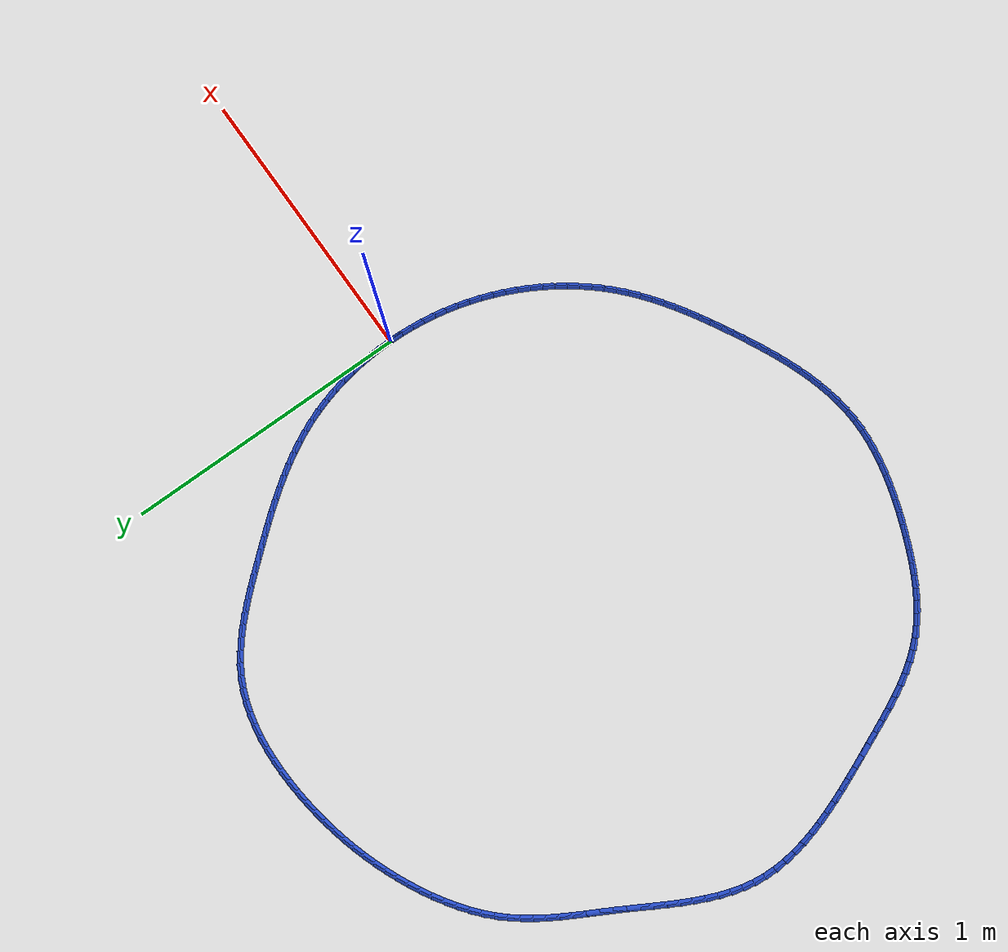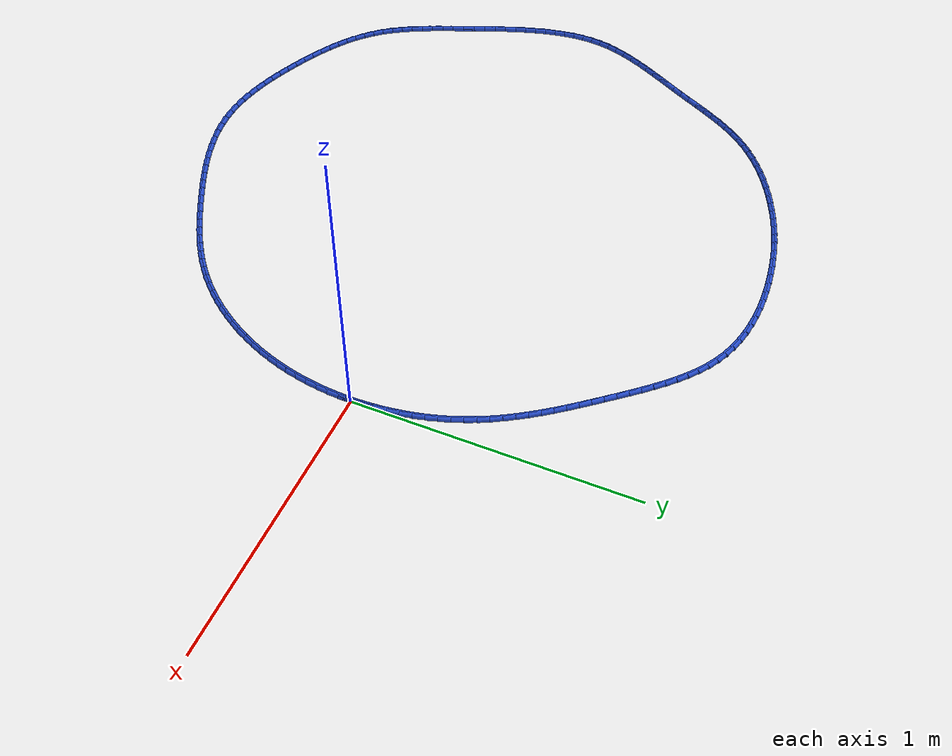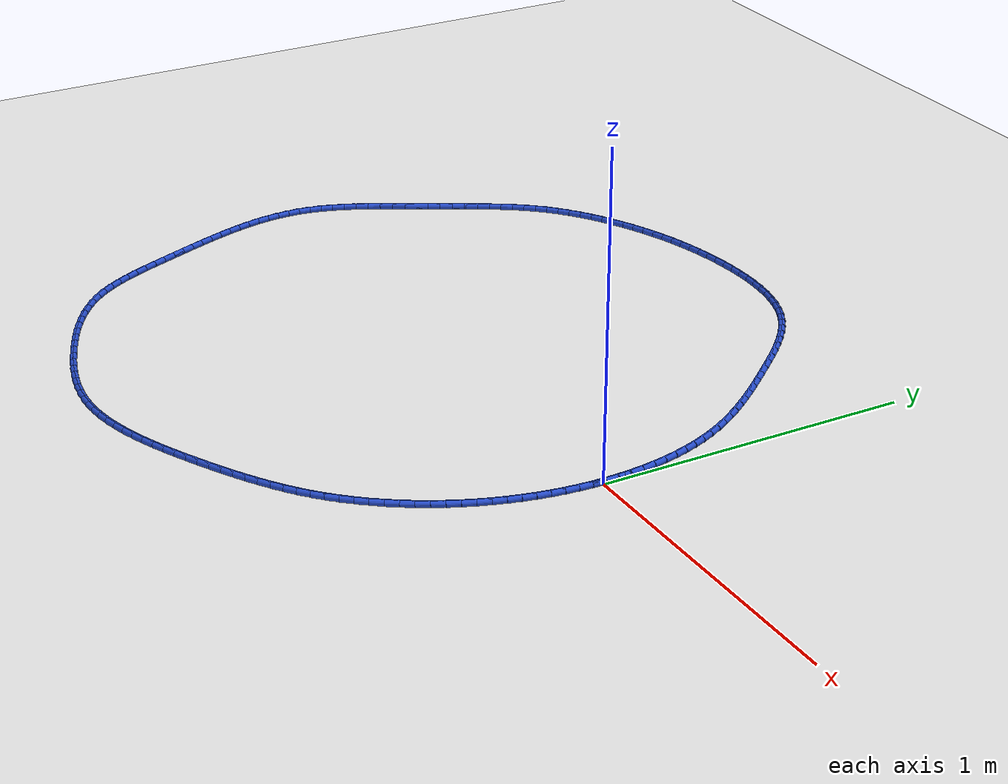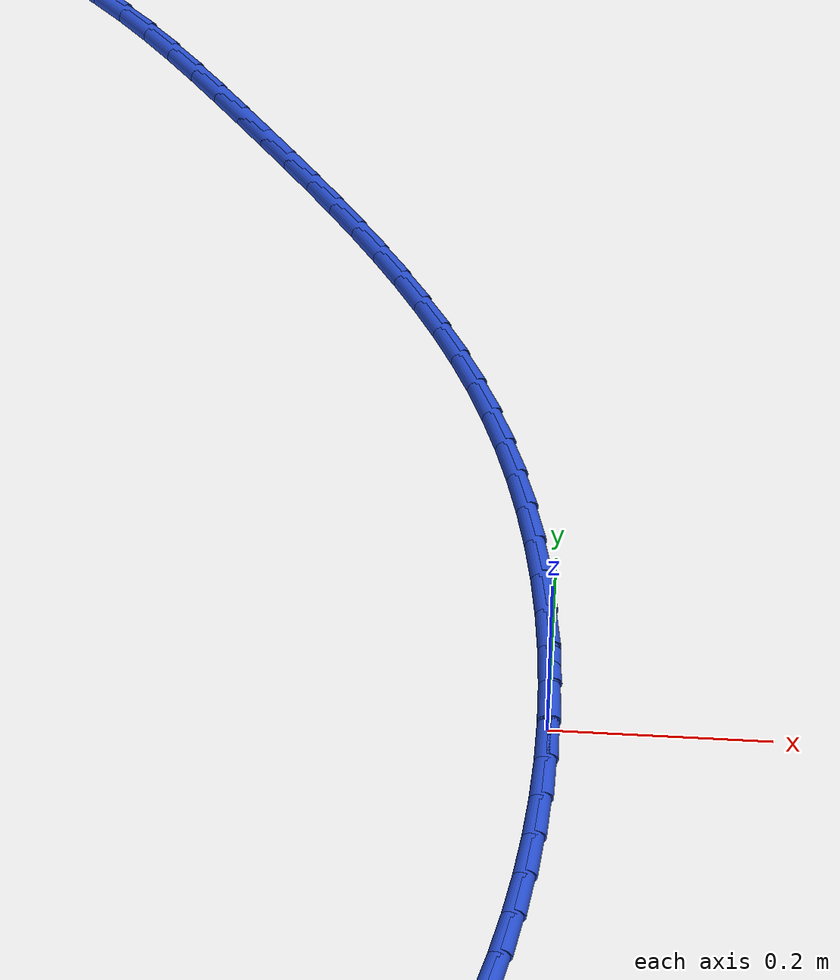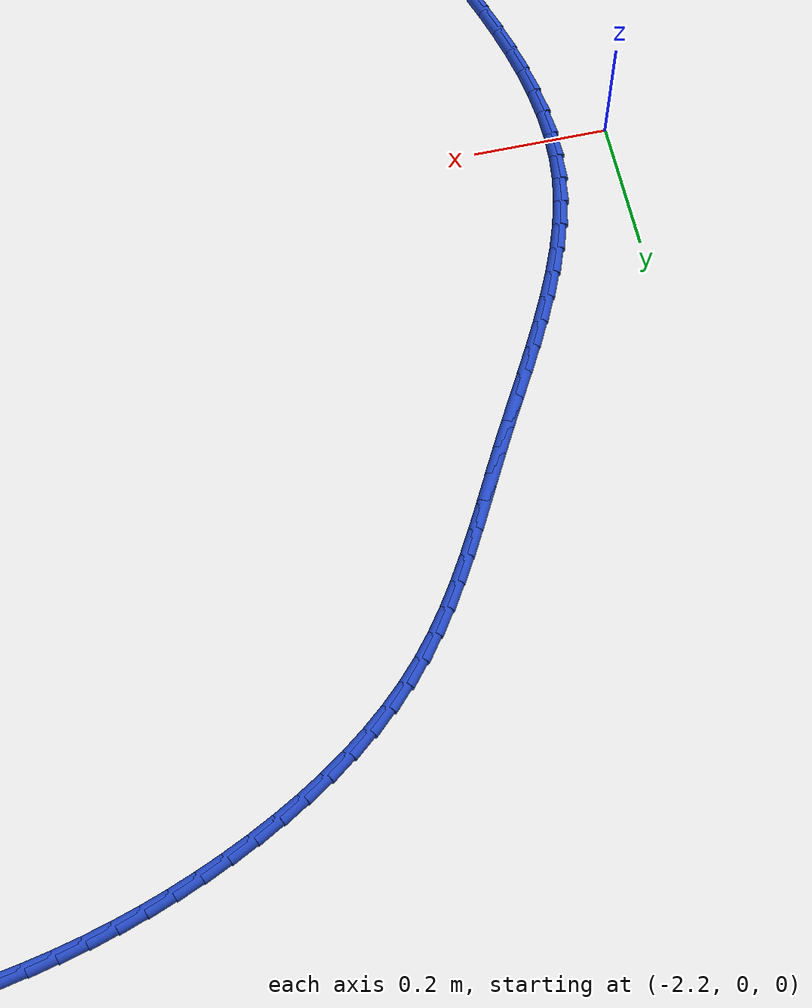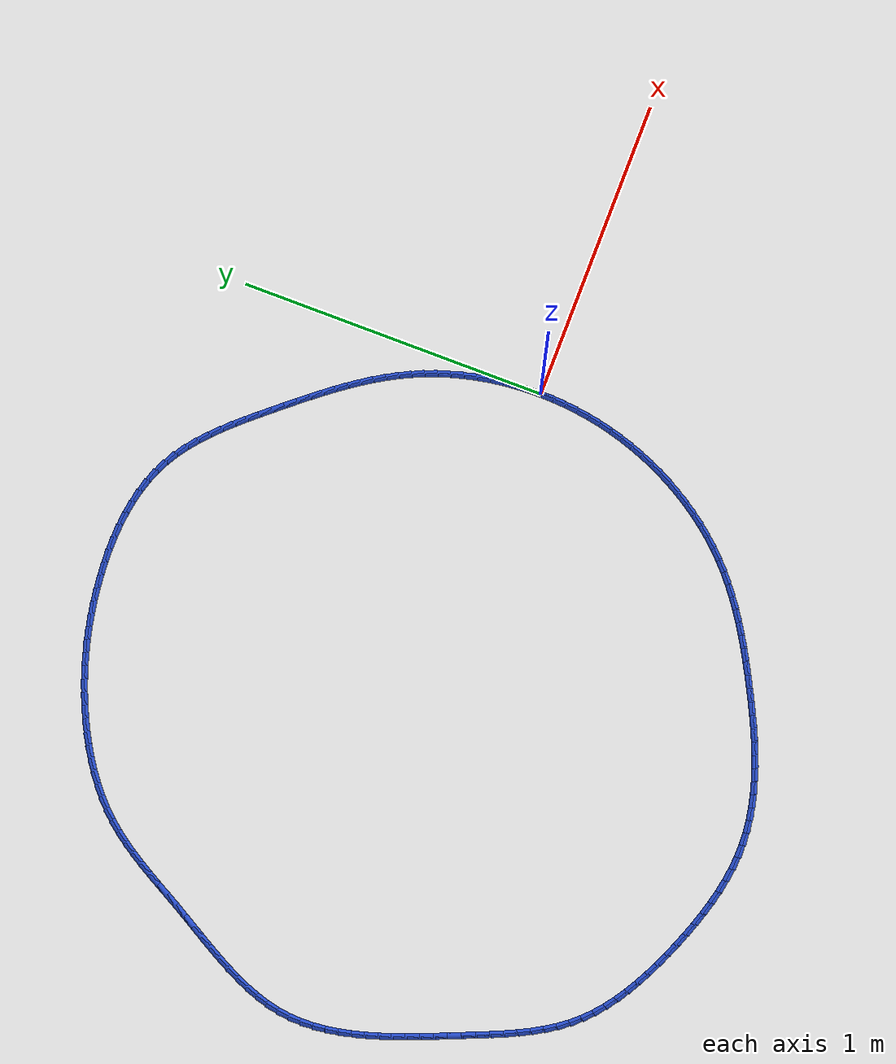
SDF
<sdf version="1.6">
 <world name="default">
  <light name="sun" type="directional">
   <pose>0 0 10 0 -0 0</pose>
   <diffuse>0.8 0.8 0.8 1</diffuse>
   <specular>0.2 0.2 0.2 1</specular>
   <attenuation>
    <range>1000</range>
    <constant>0.9</constant>
    <linear>0.01</linear>
    <quadratic>0.001</quadratic>
   </attenuation>
   <direction>-0.5 0.1 -0.9</direction>
  </light>
  <model name="ground_plane">
   <static>1</static>
   <link name="link">
    <collision name="collision">
     <geometry><plane><normal>0 0 1</normal><size>100 100</size></plane></geometry>
     <surface><friction><ode><mu>100</mu><mu2>50</mu2></ode></friction></surface>
    </collision>
    <visual name="visual">
     <cast_shadows>0</cast_shadows>
     <geometry><plane><normal>0 0 1</normal><size>100 100</size></plane></geometry>
     <material>
      <script><uri>file://media/materials/scripts/gazebo.material</uri><name>Gazebo/WhiteGlow</name></script>
     </material>
    </visual>
   </link>
  </model>
  <gravity>0 0 -9.8</gravity>
  <magnetic_field>6e-06 2.3e-05 -4.2e-05</magnetic_field>
  <atmosphere type="adiabatic"/>
  <physics name="default_physics" default="0" type="ode">
   <max_step_size>0.001</max_step_size>
   <real_time_factor>1</real_time_factor>
   <real_time_update_rate>1000</real_time_update_rate>
  </physics>
  <scene><ambient>0.4 0.4 0.4 1</ambient><background>0.7 0.7 0.7 1</background><shadows>1</shadows></scene>
  <spherical_coordinates>
   <surface_model>EARTH_WGS84</surface_model>
   <latitude_deg>0</latitude_deg>
   <longitude_deg>0</longitude_deg>
   <elevation>0</elevation>
   <heading_deg>0</heading_deg>
  </spherical_coordinates>
  <model name="line">
   <link name="link_0">
    <pose>2.42861286636753e-17 -4.163336342344337e-17 0.01 0 1.57 -1.5534062918979743</pose>
    <collision name="collision">
     <geometry><cylinder><radius>0.01</radius><length>0.08</length></cylinder></geometry>
    </collision>
    <visual name="visual">
     <material>
      <script><name>Gazebo/Blue</name><uri>file://media/materials/scripts/gazebo.material</uri></script>
     </material>
     <geometry><cylinder><radius>0.01</radius><length>0.08</length></cylinder></geometry>
    </visual>
   </link>
   <link name="link_1">
    <pose>-0.0007282638147594852 0.041874004587753304 0.01 0 1.57 -1.5122994998238044</pose>
    <collision name="collision">
     <geometry><cylinder><radius>0.01</radius><length>0.08</length></cylinder></geometry>
    </collision>
    <visual name="visual">
     <material>
      <script><name>Gazebo/Blue</name><uri>file://media/materials/scripts/gazebo.material</uri></script>
     </material>
     <geometry><cylinder><radius>0.01</radius><length>0.08</length></cylinder></geometry>
    </visual>
   </link>
   <link name="link_2">
    <pose>-0.0031798134022813576 0.08373529475296942 0.01 0 1.57 -1.470878881483492</pose>
    <collision name="collision">
     <geometry><cylinder><radius>0.01</radius><length>0.08</length></cylinder></geometry>
    </collision>
    <visual name="visual">
     <material>
      <script><name>Gazebo/Blue</name><uri>file://media/materials/scripts/gazebo.material</uri></script>
     </material>
     <geometry><cylinder><radius>0.01</radius><length>0.08</length></cylinder></geometry>
    </visual>
   </link>
   <link name="link_3">
    <pose>-0.007363573650335044 0.1254680282970825 0.01 0 1.57 -1.4289467311778268</pose>
    <collision name="collision">
     <geometry><cylinder><radius>0.01</radius><length>0.08</length></cylinder></geometry>
    </collision>
    <visual name="visual">
     <material>
      <script><name>Gazebo/Blue</name><uri>file://media/materials/scripts/gazebo.material</uri></script>
     </material>
     <geometry><cylinder><radius>0.01</radius><length>0.08</length></cylinder></geometry>
    </visual>
   </link>
   <link name="link_4">
    <pose>-0.013288469446689996 0.16695636302152658 0.01 0 1.57 -1.3863072863154795</pose>
    <collision name="collision">
     <geometry><cylinder><radius>0.01</radius><length>0.08</length></cylinder></geometry>
    </collision>
    <visual name="visual">
     <material>
      <script><name>Gazebo/Blue</name><uri>file://media/materials/scripts/gazebo.material</uri></script>
     </material>
     <geometry><cylinder><radius>0.01</radius><length>0.08</length></cylinder></geometry>
    </visual>
   </link>
   <link name="link_5">
    <pose>-0.020963425679115664 0.2080844567277358 0.01 0 1.57 -1.3427668114638152</pose>
    <collision name="collision">
     <geometry><cylinder><radius>0.01</radius><length>0.08</length></cylinder></geometry>
    </collision>
    <visual name="visual">
     <material>
      <script><name>Gazebo/Blue</name><uri>file://media/materials/scripts/gazebo.material</uri></script>
     </material>
     <geometry><cylinder><radius>0.01</radius><length>0.08</length></cylinder></geometry>
    </visual>
   </link>
   <link name="link_6">
    <pose>-0.0303973672353815 0.24873646721714424 0.01 0 1.57 -1.2981342262421736</pose>
    <collision name="collision">
     <geometry><cylinder><radius>0.01</radius><length>0.08</length></cylinder></geometry>
    </collision>
    <visual name="visual">
     <material>
      <script><name>Gazebo/Blue</name><uri>file://media/materials/scripts/gazebo.material</uri></script>
     </material>
     <geometry><cylinder><radius>0.01</radius><length>0.08</length></cylinder></geometry>
    </visual>
   </link>
   <link name="link_7">
    <pose>-0.04159921900325694 0.28879655229118595 0.01 0 1.57 -1.2522224307529084</pose>
    <collision name="collision">
     <geometry><cylinder><radius>0.01</radius><length>0.08</length></cylinder></geometry>
    </collision>
    <visual name="visual">
     <material>
      <script><name>Gazebo/Blue</name><uri>file://media/materials/scripts/gazebo.material</uri></script>
     </material>
     <geometry><cylinder><radius>0.01</radius><length>0.08</length></cylinder></geometry>
    </visual>
   </link>
   <link name="link_8">
    <pose>-0.05457790587051146 0.328148869751295 0.01 0 1.57 -1.2048504978201051</pose>
    <collision name="collision">
     <geometry><cylinder><radius>0.01</radius><length>0.08</length></cylinder></geometry>
    </collision>
    <visual name="visual">
     <material>
      <script><name>Gazebo/Blue</name><uri>file://media/materials/scripts/gazebo.material</uri></script>
     </material>
     <geometry><cylinder><radius>0.01</radius><length>0.08</length></cylinder></geometry>
    </visual>
   </link>
   <link name="link_9">
    <pose>-0.06934235272491446 0.36667757739890555 0.01 0 1.57 -1.1560197943981028</pose>
    <collision name="collision">
     <geometry><cylinder><radius>0.01</radius><length>0.08</length></cylinder></geometry>
    </collision>
    <visual name="visual">
     <material>
      <script><name>Gazebo/Blue</name><uri>file://media/materials/scripts/gazebo.material</uri></script>
     </material>
     <geometry><cylinder><radius>0.01</radius><length>0.08</length></cylinder></geometry>
    </visual>
   </link>
   <link name="link_10">
    <pose>-0.08589665054340696 0.4042734765629268 0.01 0 1.57 -1.1085103560771954</pose>
    <collision name="collision">
     <geometry><cylinder><radius>0.01</radius><length>0.08</length></cylinder></geometry>
    </collision>
    <visual name="visual">
     <material>
      <script><name>Gazebo/Blue</name><uri>file://media/materials/scripts/gazebo.material</uri></script>
     </material>
     <geometry><cylinder><radius>0.01</radius><length>0.08</length></cylinder></geometry>
    </visual>
   </link>
   <link name="link_11">
    <pose>-0.10416567340350144 0.44093624100838236 0.01 0 1.57 -1.06487421130182</pose>
    <collision name="collision">
     <geometry><cylinder><radius>0.01</radius><length>0.08</length></cylinder></geometry>
    </collision>
    <visual name="visual">
     <material>
      <script><name>Gazebo/Blue</name><uri>file://media/materials/scripts/gazebo.material</uri></script>
     </material>
     <geometry><cylinder><radius>0.01</radius><length>0.08</length></cylinder></geometry>
    </visual>
   </link>
   <link name="link_12">
    <pose>-0.12400958770196195 0.4767544760652672 0.01 0 1.57 -1.025398350004674</pose>
    <collision name="collision">
     <geometry><cylinder><radius>0.01</radius><length>0.08</length></cylinder></geometry>
    </collision>
    <visual name="visual">
     <material>
      <script><name>Gazebo/Blue</name><uri>file://media/materials/scripts/gazebo.material</uri></script>
     </material>
     <geometry><cylinder><radius>0.01</radius><length>0.08</length></cylinder></geometry>
    </visual>
   </link>
   <link name="link_13">
    <pose>-0.14528666505102436 0.5118193911772061 0.01 0 1.57 -0.9902092059021794</pose>
    <collision name="collision">
     <geometry><cylinder><radius>0.01</radius><length>0.08</length></cylinder></geometry>
    </collision>
    <visual name="visual">
     <material>
      <script><name>Gazebo/Blue</name><uri>file://media/materials/scripts/gazebo.material</uri></script>
     </material>
     <geometry><cylinder><radius>0.01</radius><length>0.08</length></cylinder></geometry>
    </visual>
   </link>
   <link name="link_14">
    <pose>-0.16785517706292458 0.5462221957878234 0.01 0 1.57 -0.9593588319528648</pose>
    <collision name="collision">
     <geometry><cylinder><radius>0.01</radius><length>0.08</length></cylinder></geometry>
    </collision>
    <visual name="visual">
     <material>
      <script><name>Gazebo/Blue</name><uri>file://media/materials/scripts/gazebo.material</uri></script>
     </material>
     <geometry><cylinder><radius>0.01</radius><length>0.08</length></cylinder></geometry>
    </visual>
   </link>
   <link name="link_15">
    <pose>-0.1915733953498984 0.5800540993407439 0.01 0 1.57 -0.9328439126575583</pose>
    <collision name="collision">
     <geometry><cylinder><radius>0.01</radius><length>0.08</length></cylinder></geometry>
    </collision>
    <visual name="visual">
     <material>
      <script><name>Gazebo/Blue</name><uri>file://media/materials/scripts/gazebo.material</uri></script>
     </material>
     <geometry><cylinder><radius>0.01</radius><length>0.08</length></cylinder></geometry>
    </visual>
   </link>
   <link name="link_16">
    <pose>-0.21629959152418177 0.6134063112795923 0.01 0 1.57 -0.9106234379059012</pose>
    <collision name="collision">
     <geometry><cylinder><radius>0.01</radius><length>0.08</length></cylinder></geometry>
    </collision>
    <visual name="visual">
     <material>
      <script><name>Gazebo/Blue</name><uri>file://media/materials/scripts/gazebo.material</uri></script>
     </material>
     <geometry><cylinder><radius>0.01</radius><length>0.08</length></cylinder></geometry>
    </visual>
   </link>
   <link name="link_17">
    <pose>-0.24189203719801064 0.6463700410479936 0.01 0 1.57 -0.8926339338847639</pose>
    <collision name="collision">
     <geometry><cylinder><radius>0.01</radius><length>0.08</length></cylinder></geometry>
    </collision>
    <visual name="visual">
     <material>
      <script><name>Gazebo/Blue</name><uri>file://media/materials/scripts/gazebo.material</uri></script>
     </material>
     <geometry><cylinder><radius>0.01</radius><length>0.08</length></cylinder></geometry>
    </visual>
   </link>
   <link name="link_18">
    <pose>-0.2682090039836207 0.6790364980895718 0.01 0 1.57 -0.8788017980443213</pose>
    <collision name="collision">
     <geometry><cylinder><radius>0.01</radius><length>0.08</length></cylinder></geometry>
    </collision>
    <visual name="visual">
     <material>
      <script><name>Gazebo/Blue</name><uri>file://media/materials/scripts/gazebo.material</uri></script>
     </material>
     <geometry><cylinder><radius>0.01</radius><length>0.08</length></cylinder></geometry>
    </visual>
   </link>
   <link name="link_19">
    <pose>-0.29510876349324805 0.711496891847952 0.01 0 1.57 -0.8690527175127222</pose>
    <collision name="collision">
     <geometry><cylinder><radius>0.01</radius><length>0.08</length></cylinder></geometry>
    </collision>
    <visual name="visual">
     <material>
      <script><name>Gazebo/Blue</name><uri>file://media/materials/scripts/gazebo.material</uri></script>
     </material>
     <geometry><cylinder><radius>0.01</radius><length>0.08</length></cylinder></geometry>
    </visual>
   </link>
   <link name="link_20">
    <pose>-0.3224495873391285 0.7438424317667587 0.01 0 1.57 -0.8633180502594889</pose>
    <collision name="collision">
     <geometry><cylinder><radius>0.01</radius><length>0.08</length></cylinder></geometry>
    </collision>
    <visual name="visual">
     <material>
      <script><name>Gazebo/Blue</name><uri>file://media/materials/scripts/gazebo.material</uri></script>
     </material>
     <geometry><cylinder><radius>0.01</radius><length>0.08</length></cylinder></geometry>
    </visual>
   </link>
   <link name="link_21">
    <pose>-0.35008975559605277 0.7761643151670784 0.01 0 1.57 -0.8592175019860075</pose>
    <collision name="collision">
     <geometry><cylinder><radius>0.01</radius><length>0.08</length></cylinder></geometry>
    </collision>
    <visual name="visual">
     <material>
      <script><name>Gazebo/Blue</name><uri>file://media/materials/scripts/gazebo.material</uri></script>
     </material>
     <geometry><cylinder><radius>0.01</radius><length>0.08</length></cylinder></geometry>
    </visual>
   </link>
   <link name="link_22">
    <pose>-0.37794610384564287 0.8084698591030915 0.01 0 1.57 -0.8488404355890604</pose>
    <collision name="collision">
     <geometry><cylinder><radius>0.01</radius><length>0.08</length></cylinder></geometry>
    </collision>
    <visual name="visual">
     <material>
      <script><name>Gazebo/Blue</name><uri>file://media/materials/scripts/gazebo.material</uri></script>
     </material>
     <geometry><cylinder><radius>0.01</radius><length>0.08</length></cylinder></geometry>
    </visual>
   </link>
   <link name="link_23">
    <pose>-0.40613394637496614 0.8404820615667923 0.01 0 1.57 -0.830407488502026</pose>
    <collision name="collision">
     <geometry><cylinder><radius>0.01</radius><length>0.08</length></cylinder></geometry>
    </collision>
    <visual name="visual">
     <material>
      <script><name>Gazebo/Blue</name><uri>file://media/materials/scripts/gazebo.material</uri></script>
     </material>
     <geometry><cylinder><radius>0.01</radius><length>0.08</length></cylinder></geometry>
    </visual>
   </link>
   <link name="link_24">
    <pose>-0.43481061021927736 0.8718637376447229 0.01 0 1.57 -0.8036621426478653</pose>
    <collision name="collision">
     <geometry><cylinder><radius>0.01</radius><length>0.08</length></cylinder></geometry>
    </collision>
    <visual name="visual">
     <material>
      <script><name>Gazebo/Blue</name><uri>file://media/materials/scripts/gazebo.material</uri></script>
     </material>
     <geometry><cylinder><radius>0.01</radius><length>0.08</length></cylinder></geometry>
    </visual>
   </link>
   <link name="link_25">
    <pose>-0.4641334224138304 0.9022777024234249 0.01 0 1.57 -0.768227353477941</pose>
    <collision name="collision">
     <geometry><cylinder><radius>0.01</radius><length>0.08</length></cylinder></geometry>
    </collision>
    <visual name="visual">
     <material>
      <script><name>Gazebo/Blue</name><uri>file://media/materials/scripts/gazebo.material</uri></script>
     </material>
     <geometry><cylinder><radius>0.01</radius><length>0.08</length></cylinder></geometry>
    </visual>
   </link>
   <link name="link_26">
    <pose>-0.4942597099938798 0.9313867709894406 0.01 0 1.57 -0.7236518108471184</pose>
    <collision name="collision">
     <geometry><cylinder><radius>0.01</radius><length>0.08</length></cylinder></geometry>
    </collision>
    <visual name="visual">
     <material>
      <script><name>Gazebo/Blue</name><uri>file://media/materials/scripts/gazebo.material</uri></script>
     </material>
     <geometry><cylinder><radius>0.01</radius><length>0.08</length></cylinder></geometry>
    </visual>
   </link>
   <link name="link_27">
    <pose>-0.52534679999468 0.9588537584293113 0.01 0 1.57 -0.6694847480080146</pose>
    <collision name="collision">
     <geometry><cylinder><radius>0.01</radius><length>0.08</length></cylinder></geometry>
    </collision>
    <visual name="visual">
     <material>
      <script><name>Gazebo/Blue</name><uri>file://media/materials/scripts/gazebo.material</uri></script>
     </material>
     <geometry><cylinder><radius>0.01</radius><length>0.08</length></cylinder></geometry>
    </visual>
   </link>
   <link name="link_28">
    <pose>-0.5575520194514852 0.9843414798295791 0.01 0 1.57 -0.6053900049680409</pose>
    <collision name="collision">
     <geometry><cylinder><radius>0.01</radius><length>0.08</length></cylinder></geometry>
    </collision>
    <visual name="visual">
     <material>
      <script><name>Gazebo/Blue</name><uri>file://media/materials/scripts/gazebo.material</uri></script>
     </material>
     <geometry><cylinder><radius>0.01</radius><length>0.08</length></cylinder></geometry>
    </visual>
   </link>
   <link name="link_29">
    <pose>-0.5910326953995494 1.0075127502767853 0.01 0 1.57 -0.5313048802138673</pose>
    <collision name="collision">
     <geometry><cylinder><radius>0.01</radius><length>0.08</length></cylinder></geometry>
    </collision>
    <visual name="visual">
     <material>
      <script><name>Gazebo/Blue</name><uri>file://media/materials/scripts/gazebo.material</uri></script>
     </material>
     <geometry><cylinder><radius>0.01</radius><length>0.08</length></cylinder></geometry>
    </visual>
   </link>
   <link name="link_30">
    <pose>-0.6259461548741271 1.0280303848574723 0.01 0 1.57 -0.44820842569968217</pose>
    <collision name="collision">
     <geometry><cylinder><radius>0.01</radius><length>0.08</length></cylinder></geometry>
    </collision>
    <visual name="visual">
     <material>
      <script><name>Gazebo/Blue</name><uri>file://media/materials/scripts/gazebo.material</uri></script>
     </material>
     <geometry><cylinder><radius>0.01</radius><length>0.08</length></cylinder></geometry>
    </visual>
   </link>
   <link name="link_31">
    <pose>-0.6624360159127359 1.0455764378285675 0.01 0 1.57 -0.36526413194980517</pose>
    <collision name="collision">
     <geometry><cylinder><radius>0.01</radius><length>0.08</length></cylinder></geometry>
    </collision>
    <visual name="visual">
     <material>
      <script><name>Gazebo/Blue</name><uri>file://media/materials/scripts/gazebo.material</uri></script>
     </material>
     <geometry><cylinder><radius>0.01</radius><length>0.08</length></cylinder></geometry>
    </visual>
   </link>
   <link name="link_32">
    <pose>-0.7004466158305225 1.0601126334743556 0.01 0 1.57 -0.28916126103859213</pose>
    <collision name="collision">
     <geometry><cylinder><radius>0.01</radius><length>0.08</length></cylinder></geometry>
    </collision>
    <visual name="visual">
     <material>
      <script><name>Gazebo/Blue</name><uri>file://media/materials/scripts/gazebo.material</uri></script>
     </material>
     <geometry><cylinder><radius>0.01</radius><length>0.08</length></cylinder></geometry>
    </visual>
   </link>
   <link name="link_33">
    <pose>-0.7397718215045112 1.0718118658854425 0.01 0 1.57 -0.21998669579418098</pose>
    <collision name="collision">
     <geometry><cylinder><radius>0.01</radius><length>0.08</length></cylinder></geometry>
    </collision>
    <visual name="visual">
     <material>
      <script><name>Gazebo/Blue</name><uri>file://media/materials/scripts/gazebo.material</uri></script>
     </material>
     <geometry><cylinder><radius>0.01</radius><length>0.08</length></cylinder></geometry>
    </visual>
   </link>
   <link name="link_34">
    <pose>-0.7802017950548022 1.080852228398294 0.01 0 1.57 -0.15741870087668922</pose>
    <collision name="collision">
     <geometry><cylinder><radius>0.01</radius><length>0.08</length></cylinder></geometry>
    </collision>
    <visual name="visual">
     <material>
      <script><name>Gazebo/Blue</name><uri>file://media/materials/scripts/gazebo.material</uri></script>
     </material>
     <geometry><cylinder><radius>0.01</radius><length>0.08</length></cylinder></geometry>
    </visual>
   </link>
   <link name="link_35">
    <pose>-0.8215266986014952 1.087411814349373 0.01 0 1.57 -0.10098601371394565</pose>
    <collision name="collision">
     <geometry><cylinder><radius>0.01</radius><length>0.08</length></cylinder></geometry>
    </collision>
    <visual name="visual">
     <material>
      <script><name>Gazebo/Blue</name><uri>file://media/materials/scripts/gazebo.material</uri></script>
     </material>
     <geometry><cylinder><radius>0.01</radius><length>0.08</length></cylinder></geometry>
    </visual>
   </link>
   <link name="link_36">
    <pose>-0.8635366942646903 1.0916687170751453 0.01 0 1.57 -0.05014740697422647</pose>
    <collision name="collision">
     <geometry><cylinder><radius>0.01</radius><length>0.08</length></cylinder></geometry>
    </collision>
    <visual name="visual">
     <material>
      <script><name>Gazebo/Blue</name><uri>file://media/materials/scripts/gazebo.material</uri></script>
     </material>
     <geometry><cylinder><radius>0.01</radius><length>0.08</length></cylinder></geometry>
    </visual>
   </link>
   <link name="link_37">
    <pose>-0.906021944164487 1.0938010299120742 0.01 0 1.57 -0.004346484644055701</pose>
    <collision name="collision">
     <geometry><cylinder><radius>0.01</radius><length>0.08</length></cylinder></geometry>
    </collision>
    <visual name="visual">
     <material>
      <script><name>Gazebo/Blue</name><uri>file://media/materials/scripts/gazebo.material</uri></script>
     </material>
     <geometry><cylinder><radius>0.01</radius><length>0.08</length></cylinder></geometry>
    </visual>
   </link>
   <link name="link_38">
    <pose>-0.9487726104209857 1.0939868461966253 0.01 0 1.57 0.03695410515328859</pose>
    <collision name="collision">
     <geometry><cylinder><radius>0.01</radius><length>0.08</length></cylinder></geometry>
    </collision>
    <visual name="visual">
     <material>
      <script><name>Gazebo/Blue</name><uri>file://media/materials/scripts/gazebo.material</uri></script>
     </material>
     <geometry><cylinder><radius>0.01</radius><length>0.08</length></cylinder></geometry>
    </visual>
   </link>
   <link name="link_39">
    <pose>-0.9915788551542861 1.0924042592652627 0.01 0 1.57 0.07425359649814745</pose>
    <collision name="collision">
     <geometry><cylinder><radius>0.01</radius><length>0.08</length></cylinder></geometry>
    </collision>
    <visual name="visual">
     <material>
      <script><name>Gazebo/Blue</name><uri>file://media/materials/scripts/gazebo.material</uri></script>
     </material>
     <geometry><cylinder><radius>0.01</radius><length>0.08</length></cylinder></geometry>
    </visual>
   </link>
   <link name="link_40">
    <pose>-1.0342308404844875 1.0892313624544507 0.01 0 1.57 0.10800493814997753</pose>
    <collision name="collision">
     <geometry><cylinder><radius>0.01</radius><length>0.08</length></cylinder></geometry>
    </collision>
    <visual name="visual">
     <material>
      <script><name>Gazebo/Blue</name><uri>file://media/materials/scripts/gazebo.material</uri></script>
     </material>
     <geometry><cylinder><radius>0.01</radius><length>0.08</length></cylinder></geometry>
    </visual>
   </link>
   <link name="link_41">
    <pose>-1.076518770796116 1.084646214591214 0.01 0 1.57 0.1394423321948671</pose>
    <collision name="collision">
     <geometry><cylinder><radius>0.01</radius><length>0.08</length></cylinder></geometry>
    </collision>
    <visual name="visual">
     <material>
      <script><name>Gazebo/Blue</name><uri>file://media/materials/scripts/gazebo.material</uri></script>
     </material>
     <geometry><cylinder><radius>0.01</radius><length>0.08</length></cylinder></geometry>
    </visual>
   </link>
   <link name="link_42">
    <pose>-1.1182851522714998 1.0787841694192992 0.01 0 1.57 0.17118040340994842</pose>
    <collision name="collision">
     <geometry><cylinder><radius>0.01</radius><length>0.08</length></cylinder></geometry>
    </collision>
    <visual name="visual">
     <material>
      <script><name>Gazebo/Blue</name><uri>file://media/materials/scripts/gazebo.material</uri></script>
     </material>
     <geometry><cylinder><radius>0.01</radius><length>0.08</length></cylinder></geometry>
    </visual>
   </link>
   <link name="link_43">
    <pose>-1.1595267264960334 1.0716546455137161 0.01 0 1.57 0.20357888360128518</pose>
    <collision name="collision">
     <geometry><cylinder><radius>0.01</radius><length>0.08</length></cylinder></geometry>
    </collision>
    <visual name="visual">
     <material>
      <script><name>Gazebo/Blue</name><uri>file://media/materials/scripts/gazebo.material</uri></script>
     </material>
     <geometry><cylinder><radius>0.01</radius><length>0.08</length></cylinder></geometry>
    </visual>
   </link>
   <link name="link_44">
    <pose>-1.2002685263221498 1.0632439612700235 0.01 0 1.57 0.23651764979526615</pose>
    <collision name="collision">
     <geometry><cylinder><radius>0.01</radius><length>0.08</length></cylinder></geometry>
    </collision>
    <visual name="visual">
     <material>
      <script><name>Gazebo/Blue</name><uri>file://media/materials/scripts/gazebo.material</uri></script>
     </material>
     <geometry><cylinder><radius>0.01</radius><length>0.08</length></cylinder></geometry>
    </visual>
   </link>
   <link name="link_45">
    <pose>-1.2405355846022805 1.0535384350837784 0.01 0 1.57 0.2698664262997794</pose>
    <collision name="collision">
     <geometry><cylinder><radius>0.01</radius><length>0.08</length></cylinder></geometry>
    </collision>
    <visual name="visual">
     <material>
      <script><name>Gazebo/Blue</name><uri>file://media/materials/scripts/gazebo.material</uri></script>
     </material>
     <geometry><cylinder><radius>0.01</radius><length>0.08</length></cylinder></geometry>
    </visual>
   </link>
   <link name="link_46">
    <pose>-1.2803529341888598 1.0425243853505397 0.01 0 1.57 0.30348708083744264</pose>
    <collision name="collision">
     <geometry><cylinder><radius>0.01</radius><length>0.08</length></cylinder></geometry>
    </collision>
    <visual name="visual">
     <material>
      <script><name>Gazebo/Blue</name><uri>file://media/materials/scripts/gazebo.material</uri></script>
     </material>
     <geometry><cylinder><radius>0.01</radius><length>0.08</length></cylinder></geometry>
    </visual>
   </link>
   <link name="link_47">
    <pose>-1.3197456079343197 1.0301881304658655 0.01 0 1.57 0.33723630496613444</pose>
    <collision name="collision">
     <geometry><cylinder><radius>0.01</radius><length>0.08</length></cylinder></geometry>
    </collision>
    <visual name="visual">
     <material>
      <script><name>Gazebo/Blue</name><uri>file://media/materials/scripts/gazebo.material</uri></script>
     </material>
     <geometry><cylinder><radius>0.01</radius><length>0.08</length></cylinder></geometry>
    </visual>
   </link>
   <link name="link_48">
    <pose>-1.3587386386910945 1.0165159888253141 0.01 0 1.57 0.37096855601701206</pose>
    <collision name="collision">
     <geometry><cylinder><radius>0.01</radius><length>0.08</length></cylinder></geometry>
    </collision>
    <visual name="visual">
     <material>
      <script><name>Gazebo/Blue</name><uri>file://media/materials/scripts/gazebo.material</uri></script>
     </material>
     <geometry><cylinder><radius>0.01</radius><length>0.08</length></cylinder></geometry>
    </visual>
   </link>
   <link name="link_49">
    <pose>-1.3973570593116145 1.0014942788244432 0.01 0 1.57 0.40453911349773936</pose>
    <collision name="collision">
     <geometry><cylinder><radius>0.01</radius><length>0.08</length></cylinder></geometry>
    </collision>
    <visual name="visual">
     <material>
      <script><name>Gazebo/Blue</name><uri>file://media/materials/scripts/gazebo.material</uri></script>
     </material>
     <geometry><cylinder><radius>0.01</radius><length>0.08</length></cylinder></geometry>
    </visual>
   </link>
   <link name="link_50">
    <pose>-1.4356259026483147 0.9851093188588111 0.01 0 1.57 0.43810907245205244</pose>
    <collision name="collision">
     <geometry><cylinder><radius>0.01</radius><length>0.08</length></cylinder></geometry>
    </collision>
    <visual name="visual">
     <material>
      <script><name>Gazebo/Blue</name><uri>file://media/materials/scripts/gazebo.material</uri></script>
     </material>
     <geometry><cylinder><radius>0.01</radius><length>0.08</length></cylinder></geometry>
    </visual>
   </link>
   <link name="link_51">
    <pose>-1.4735444292242035 0.9673455297504959 0.01 0 1.57 0.47349772439308224</pose>
    <collision name="collision">
     <geometry><cylinder><radius>0.01</radius><length>0.08</length></cylinder></geometry>
    </collision>
    <visual name="visual">
     <material>
      <script><name>Gazebo/Blue</name><uri>file://media/materials/scripts/gazebo.material</uri></script>
     </material>
     <geometry><cylinder><radius>0.01</radius><length>0.08</length></cylinder></geometry>
    </visual>
   </link>
   <link name="link_52">
    <pose>-1.5109576388553578 0.9481759743639133 0.01 0 1.57 0.5116668210867137</pose>
    <collision name="collision">
     <geometry><cylinder><radius>0.01</radius><length>0.08</length></cylinder></geometry>
    </collision>
    <visual name="visual">
     <material>
      <script><name>Gazebo/Blue</name><uri>file://media/materials/scripts/gazebo.material</uri></script>
     </material>
     <geometry><cylinder><radius>0.01</radius><length>0.08</length></cylinder></geometry>
    </visual>
   </link>
   <link name="link_53">
    <pose>-1.5476533900152138 0.9275695083420579 0.01 0 1.57 0.5529649195357228</pose>
    <collision name="collision">
     <geometry><cylinder><radius>0.01</radius><length>0.08</length></cylinder></geometry>
    </collision>
    <visual name="visual">
     <material>
      <script><name>Gazebo/Blue</name><uri>file://media/materials/scripts/gazebo.material</uri></script>
     </material>
     <geometry><cylinder><radius>0.01</radius><length>0.08</length></cylinder></geometry>
    </visual>
   </link>
   <link name="link_54">
    <pose>-1.5834194481565473 0.9054949804789695 0.01 0 1.57 0.5977557230571702</pose>
    <collision name="collision">
     <geometry><cylinder><radius>0.01</radius><length>0.08</length></cylinder></geometry>
    </collision>
    <visual name="visual">
     <material>
      <script><name>Gazebo/Blue</name><uri>file://media/materials/scripts/gazebo.material</uri></script>
     </material>
     <geometry><cylinder><radius>0.01</radius><length>0.08</length></cylinder></geometry>
    </visual>
   </link>
   <link name="link_55">
    <pose>-1.6180435787321352 0.8819212395686875 0.01 0 1.57 0.6464115516235832</pose>
    <collision name="collision">
     <geometry><cylinder><radius>0.01</radius><length>0.08</length></cylinder></geometry>
    </collision>
    <visual name="visual">
     <material>
      <script><name>Gazebo/Blue</name><uri>file://media/materials/scripts/gazebo.material</uri></script>
     </material>
     <geometry><cylinder><radius>0.01</radius><length>0.08</length></cylinder></geometry>
    </visual>
   </link>
   <link name="link_56">
    <pose>-1.6513135471947535 0.8568171344052513 0.01 0 1.57 0.6992997245450739</pose>
    <collision name="collision">
     <geometry><cylinder><radius>0.01</radius><length>0.08</length></cylinder></geometry>
    </collision>
    <visual name="visual">
     <material>
      <script><name>Gazebo/Blue</name><uri>file://media/materials/scripts/gazebo.material</uri></script>
     </material>
     <geometry><cylinder><radius>0.01</radius><length>0.08</length></cylinder></geometry>
    </visual>
   </link>
   <link name="link_57">
    <pose>-1.683017118997179 0.8301515137827008 0.01 0 1.57 0.7567610845434604</pose>
    <collision name="collision">
     <geometry><cylinder><radius>0.01</radius><length>0.08</length></cylinder></geometry>
    </collision>
    <visual name="visual">
     <material>
      <script><name>Gazebo/Blue</name><uri>file://media/materials/scripts/gazebo.material</uri></script>
     </material>
     <geometry><cylinder><radius>0.01</radius><length>0.08</length></cylinder></geometry>
    </visual>
   </link>
   <link name="link_58">
    <pose>-1.7129420595921874 0.8018932264950751 0.01 0 1.57 0.8190586255264551</pose>
    <collision name="collision">
     <geometry><cylinder><radius>0.01</radius><length>0.08</length></cylinder></geometry>
    </collision>
    <visual name="visual">
     <material>
      <script><name>Gazebo/Blue</name><uri>file://media/materials/scripts/gazebo.material</uri></script>
     </material>
     <geometry><cylinder><radius>0.01</radius><length>0.08</length></cylinder></geometry>
    </visual>
   </link>
   <link name="link_59">
    <pose>-1.7408769503276151 0.7720114651922916 0.01 0 1.57 0.8824137669769075</pose>
    <collision name="collision">
     <geometry><cylinder><radius>0.01</radius><length>0.08</length></cylinder></geometry>
    </collision>
    <visual name="visual">
     <material>
      <script><name>Gazebo/Blue</name><uri>file://media/materials/scripts/gazebo.material</uri></script>
     </material>
     <geometry><cylinder><radius>0.01</radius><length>0.08</length></cylinder></geometry>
    </visual>
   </link>
   <link name="link_60">
    <pose>-1.76676539973835 0.74054075814405 0.01 0 1.57 0.9378704573168014</pose>
    <collision name="collision">
     <geometry><cylinder><radius>0.01</radius><length>0.08</length></cylinder></geometry>
    </collision>
    <visual name="visual">
     <material>
      <script><name>Gazebo/Blue</name><uri>file://media/materials/scripts/gazebo.material</uri></script>
     </material>
     <geometry><cylinder><radius>0.01</radius><length>0.08</length></cylinder></geometry>
    </visual>
   </link>
   <link name="link_61">
    <pose>-1.790888480675045 0.7076578566755316 0.01 0 1.57 0.9838079836002007</pose>
    <collision name="collision">
     <geometry><cylinder><radius>0.01</radius><length>0.08</length></cylinder></geometry>
    </collision>
    <visual name="visual">
     <material>
      <script><name>Gazebo/Blue</name><uri>file://media/materials/scripts/gazebo.material</uri></script>
     </material>
     <geometry><cylinder><radius>0.01</radius><length>0.08</length></cylinder></geometry>
    </visual>
   </link>
   <link name="link_62">
    <pose>-1.813571649776204 0.673558217490909 0.01 0 1.57 1.0200538556029488</pose>
    <collision name="collision">
     <geometry><cylinder><radius>0.01</radius><length>0.08</length></cylinder></geometry>
    </collision>
    <visual name="visual">
     <material>
      <script><name>Gazebo/Blue</name><uri>file://media/materials/scripts/gazebo.material</uri></script>
     </material>
     <geometry><cylinder><radius>0.01</radius><length>0.08</length></cylinder></geometry>
    </visual>
   </link>
   <link name="link_63">
    <pose>-1.835140363680332 0.6384372972943543 0.01 0 1.57 1.0466583227039368</pose>
    <collision name="collision">
     <geometry><cylinder><radius>0.01</radius><length>0.08</length></cylinder></geometry>
    </collision>
    <visual name="visual">
     <material>
      <script><name>Gazebo/Blue</name><uri>file://media/materials/scripts/gazebo.material</uri></script>
     </material>
     <geometry><cylinder><radius>0.01</radius><length>0.08</length></cylinder></geometry>
    </visual>
   </link>
   <link name="link_64">
    <pose>-1.8559200790259354 0.6024905527900405 0.01 0 1.57 1.0637906776533215</pose>
    <collision name="collision">
     <geometry><cylinder><radius>0.01</radius><length>0.08</length></cylinder></geometry>
    </collision>
    <visual name="visual">
     <material>
      <script><name>Gazebo/Blue</name><uri>file://media/materials/scripts/gazebo.material</uri></script>
     </material>
     <geometry><cylinder><radius>0.01</radius><length>0.08</length></cylinder></geometry>
    </visual>
   </link>
   <link name="link_65">
    <pose>-1.8762362524515184 0.5659134406821397 0.01 0 1.57 1.0716638578407824</pose>
    <collision name="collision">
     <geometry><cylinder><radius>0.01</radius><length>0.08</length></cylinder></geometry>
    </collision>
    <visual name="visual">
     <material>
      <script><name>Gazebo/Blue</name><uri>file://media/materials/scripts/gazebo.material</uri></script>
     </material>
     <geometry><cylinder><radius>0.01</radius><length>0.08</length></cylinder></geometry>
    </visual>
   </link>
   <link name="link_66">
    <pose>-1.8964143405955864 0.5289014176748237 0.01 0 1.57 1.0704886454675888</pose>
    <collision name="collision">
     <geometry><cylinder><radius>0.01</radius><length>0.08</length></cylinder></geometry>
    </collision>
    <visual name="visual">
     <material>
      <script><name>Gazebo/Blue</name><uri>file://media/materials/scripts/gazebo.material</uri></script>
     </material>
     <geometry><cylinder><radius>0.01</radius><length>0.08</length></cylinder></geometry>
    </visual>
   </link>
   <link name="link_67">
    <pose>-1.916779800096645 0.4916499404722658 0.01 0 1.57 1.06092664789406</pose>
    <collision name="collision">
     <geometry><cylinder><radius>0.01</radius><length>0.08</length></cylinder></geometry>
    </collision>
    <visual name="visual">
     <material>
      <script><name>Gazebo/Blue</name><uri>file://media/materials/scripts/gazebo.material</uri></script>
     </material>
     <geometry><cylinder><radius>0.01</radius><length>0.08</length></cylinder></geometry>
    </visual>
   </link>
   <link name="link_68">
    <pose>-1.9376385767630275 0.4543480126797631 0.01 0 1.57 1.0517392426218832</pose>
    <collision name="collision">
     <geometry><cylinder><radius>0.01</radius><length>0.08</length></cylinder></geometry>
    </collision>
    <visual name="visual">
     <material>
      <script><name>Gazebo/Blue</name><uri>file://media/materials/scripts/gazebo.material</uri></script>
     </material>
     <geometry><cylinder><radius>0.01</radius><length>0.08</length></cylinder></geometry>
    </visual>
   </link>
   <link name="link_69">
    <pose>-1.9589381391680638 0.4170660735452046 0.01 0 1.57 1.0504066511306098</pose>
    <collision name="collision">
     <geometry><cylinder><radius>0.01</radius><length>0.08</length></cylinder></geometry>
    </collision>
    <visual name="visual">
     <material>
      <script><name>Gazebo/Blue</name><uri>file://media/materials/scripts/gazebo.material</uri></script>
     </material>
     <geometry><cylinder><radius>0.01</radius><length>0.08</length></cylinder></geometry>
    </visual>
   </link>
   <link name="link_70">
    <pose>-1.9803114409524911 0.37977053824678153 0.01 0 1.57 1.05714541838875</pose>
    <collision name="collision">
     <geometry><cylinder><radius>0.01</radius><length>0.08</length></cylinder></geometry>
    </collision>
    <visual name="visual">
     <material>
      <script><name>Gazebo/Blue</name><uri>file://media/materials/scripts/gazebo.material</uri></script>
     </material>
     <geometry><cylinder><radius>0.01</radius><length>0.08</length></cylinder></geometry>
    </visual>
   </link>
   <link name="link_71">
    <pose>-2.001380764594178 0.342424292534748 0.01 0 1.57 1.0720871526071907</pose>
    <collision name="collision">
     <geometry><cylinder><radius>0.01</radius><length>0.08</length></cylinder></geometry>
    </collision>
    <visual name="visual">
     <material>
      <script><name>Gazebo/Blue</name><uri>file://media/materials/scripts/gazebo.material</uri></script>
     </material>
     <geometry><cylinder><radius>0.01</radius><length>0.08</length></cylinder></geometry>
    </visual>
   </link>
   <link name="link_72">
    <pose>-2.021768392570992 0.3049902221593582 0.01 0 1.57 1.0955297165146125</pose>
    <collision name="collision">
     <geometry><cylinder><radius>0.01</radius><length>0.08</length></cylinder></geometry>
    </collision>
    <visual name="visual">
     <material>
      <script><name>Gazebo/Blue</name><uri>file://media/materials/scripts/gazebo.material</uri></script>
     </material>
     <geometry><cylinder><radius>0.01</radius><length>0.08</length></cylinder></geometry>
    </visual>
   </link>
   <link name="link_73">
    <pose>-2.0410966073608003 0.26743121287086524 0.01 0 1.57 1.1279196252805543</pose>
    <collision name="collision">
     <geometry><cylinder><radius>0.01</radius><length>0.08</length></cylinder></geometry>
    </collision>
    <visual name="visual">
     <material>
      <script><name>Gazebo/Blue</name><uri>file://media/materials/scripts/gazebo.material</uri></script>
     </material>
     <geometry><cylinder><radius>0.01</radius><length>0.08</length></cylinder></geometry>
    </visual>
   </link>
   <link name="link_74">
    <pose>-2.05898769144147 0.2297101504195236 0.01 0 1.57 1.1698163942049855</pose>
    <collision name="collision">
     <geometry><cylinder><radius>0.01</radius><length>0.08</length></cylinder></geometry>
    </collision>
    <visual name="visual">
     <material>
      <script><name>Gazebo/Blue</name><uri>file://media/materials/scripts/gazebo.material</uri></script>
     </material>
     <geometry><cylinder><radius>0.01</radius><length>0.08</length></cylinder></geometry>
    </visual>
   </link>
   <link name="link_75">
    <pose>-2.0750639272908704 0.19178992055558672 0.01 0 1.57 1.221826851463844</pose>
    <collision name="collision">
     <geometry><cylinder><radius>0.01</radius><length>0.08</length></cylinder></geometry>
    </collision>
    <visual name="visual">
     <material>
      <script><name>Gazebo/Blue</name><uri>file://media/materials/scripts/gazebo.material</uri></script>
     </material>
     <geometry><cylinder><radius>0.01</radius><length>0.08</length></cylinder></geometry>
    </visual>
   </link>
   <link name="link_76">
    <pose>-2.0889475973868685 0.1536334090293082 0.01 0 1.57 1.2844940822434423</pose>
    <collision name="collision">
     <geometry><cylinder><radius>0.01</radius><length>0.08</length></cylinder></geometry>
    </collision>
    <visual name="visual">
     <material>
      <script><name>Gazebo/Blue</name><uri>file://media/materials/scripts/gazebo.material</uri></script>
     </material>
     <geometry><cylinder><radius>0.01</radius><length>0.08</length></cylinder></geometry>
    </visual>
   </link>
   <link name="link_77">
    <pose>-2.1002609842073316 0.11520350159094228 0.01 0 1.57 1.3581272919895013</pose>
    <collision name="collision">
     <geometry><cylinder><radius>0.01</radius><length>0.08</length></cylinder></geometry>
    </collision>
    <visual name="visual">
     <material>
      <script><name>Gazebo/Blue</name><uri>file://media/materials/scripts/gazebo.material</uri></script>
     </material>
     <geometry><cylinder><radius>0.01</radius><length>0.08</length></cylinder></geometry>
    </visual>
   </link>
   <link name="link_78">
    <pose>-2.108626370230128 0.07646308399074223 0.01 0 1.57 1.4419773215086646</pose>
    <collision name="collision">
     <geometry><cylinder><radius>0.01</radius><length>0.08</length></cylinder></geometry>
    </collision>
    <visual name="visual">
     <material>
      <script><name>Gazebo/Blue</name><uri>file://media/materials/scripts/gazebo.material</uri></script>
     </material>
     <geometry><cylinder><radius>0.01</radius><length>0.08</length></cylinder></geometry>
    </visual>
   </link>
   <link name="link_79">
    <pose>-2.113689323164126 0.03737788500122309 0.01 0 1.57 1.526290605137046</pose>
    <collision name="collision">
     <geometry><cylinder><radius>0.01</radius><length>0.08</length></cylinder></geometry>
    </collision>
    <visual name="visual">
     <material>
      <script><name>Gazebo/Blue</name><uri>file://media/materials/scripts/gazebo.material</uri></script>
     </material>
     <geometry><cylinder><radius>0.01</radius><length>0.08</length></cylinder></geometry>
    </visual>
   </link>
   <link name="link_80">
    <pose>-2.115444968008097 -0.002043687227925963 0.01 0 1.57 -1.5384065185165545</pose>
    <collision name="collision">
     <geometry><cylinder><radius>0.01</radius><length>0.08</length></cylinder></geometry>
    </collision>
    <visual name="visual">
     <material>
      <script><name>Gazebo/Blue</name><uri>file://media/materials/scripts/gazebo.material</uri></script>
     </material>
     <geometry><cylinder><radius>0.01</radius><length>0.08</length></cylinder></geometry>
    </visual>
   </link>
   <link name="link_81">
    <pose>-2.11415810453712 -0.04176029846644008 0.01 0 1.57 -1.4696254007020295</pose>
    <collision name="collision">
     <geometry><cylinder><radius>0.01</radius><length>0.08</length></cylinder></geometry>
    </collision>
    <visual name="visual">
     <material>
      <script><name>Gazebo/Blue</name><uri>file://media/materials/scripts/gazebo.material</uri></script>
     </material>
     <geometry><cylinder><radius>0.01</radius><length>0.08</length></cylinder></geometry>
    </visual>
   </link>
   <link name="link_82">
    <pose>-2.1101005033658335 -0.08172976337581278 0.01 0 1.57 -1.4090426154863513</pose>
    <collision name="collision">
     <geometry><cylinder><radius>0.01</radius><length>0.08</length></cylinder></geometry>
    </collision>
    <visual name="visual">
     <material>
      <script><name>Gazebo/Blue</name><uri>file://media/materials/scripts/gazebo.material</uri></script>
     </material>
     <geometry><cylinder><radius>0.01</radius><length>0.08</length></cylinder></geometry>
    </visual>
   </link>
   <link name="link_83">
    <pose>-2.103543935108875 -0.12190989661753537 0.01 0 1.57 -1.3564439498817953</pose>
    <collision name="collision">
     <geometry><cylinder><radius>0.01</radius><length>0.08</length></cylinder></geometry>
    </collision>
    <visual name="visual">
     <material>
      <script><name>Gazebo/Blue</name><uri>file://media/materials/scripts/gazebo.material</uri></script>
     </material>
     <geometry><cylinder><radius>0.01</radius><length>0.08</length></cylinder></geometry>
    </visual>
   </link>
   <link name="link_84">
    <pose>-2.0947601703808822 -0.16225851285310147 0.01 0 1.57 -1.311442697950577</pose>
    <collision name="collision">
     <geometry><cylinder><radius>0.01</radius><length>0.08</length></cylinder></geometry>
    </collision>
    <visual name="visual">
     <material>
      <script><name>Gazebo/Blue</name><uri>file://media/materials/scripts/gazebo.material</uri></script>
     </material>
     <geometry><cylinder><radius>0.01</radius><length>0.08</length></cylinder></geometry>
    </visual>
   </link>
   <link name="link_85">
    <pose>-2.0840209797964926 -0.20273342674400385 0.01 0 1.57 -1.2735784377788513</pose>
    <collision name="collision">
     <geometry><cylinder><radius>0.01</radius><length>0.08</length></cylinder></geometry>
    </collision>
    <visual name="visual">
     <material>
      <script><name>Gazebo/Blue</name><uri>file://media/materials/scripts/gazebo.material</uri></script>
     </material>
     <geometry><cylinder><radius>0.01</radius><length>0.08</length></cylinder></geometry>
    </visual>
   </link>
   <link name="link_86">
    <pose>-2.071598133970342 -0.24329245295173527 0.01 0 1.57 -1.2423866683645894</pose>
    <collision name="collision">
     <geometry><cylinder><radius>0.01</radius><length>0.08</length></cylinder></geometry>
    </collision>
    <visual name="visual">
     <material>
      <script><name>Gazebo/Blue</name><uri>file://media/materials/scripts/gazebo.material</uri></script>
     </material>
     <geometry><cylinder><radius>0.01</radius><length>0.08</length></cylinder></geometry>
    </visual>
   </link>
   <link name="link_87">
    <pose>-2.057763403517069 -0.28389340613778924 0.01 0 1.57 -1.2174439581185321</pose>
    <collision name="collision">
     <geometry><cylinder><radius>0.01</radius><length>0.08</length></cylinder></geometry>
    </collision>
    <visual name="visual">
     <material>
      <script><name>Gazebo/Blue</name><uri>file://media/materials/scripts/gazebo.material</uri></script>
     </material>
     <geometry><cylinder><radius>0.01</radius><length>0.08</length></cylinder></geometry>
    </visual>
   </link>
   <link name="link_88">
    <pose>-2.0427885590513113 -0.32449410096365716 0.01 0 1.57 -1.1983952913517646</pose>
    <collision name="collision">
     <geometry><cylinder><radius>0.01</radius><length>0.08</length></cylinder></geometry>
    </collision>
    <visual name="visual">
     <material>
      <script><name>Gazebo/Blue</name><uri>file://media/materials/scripts/gazebo.material</uri></script>
     </material>
     <geometry><cylinder><radius>0.01</radius><length>0.08</length></cylinder></geometry>
    </visual>
   </link>
   <link name="link_89">
    <pose>-2.026945371187706 -0.36505235209083253 0.01 0 1.57 -1.1849698228149663</pose>
    <collision name="collision">
     <geometry><cylinder><radius>0.01</radius><length>0.08</length></cylinder></geometry>
    </collision>
    <visual name="visual">
     <material>
      <script><name>Gazebo/Blue</name><uri>file://media/materials/scripts/gazebo.material</uri></script>
     </material>
     <geometry><cylinder><radius>0.01</radius><length>0.08</length></cylinder></geometry>
    </visual>
   </link>
   <link name="link_90">
    <pose>-2.0105056105408896 -0.40552597418080816 0.01 0 1.57 -1.1769898899506765</pose>
    <collision name="collision">
     <geometry><cylinder><radius>0.01</radius><length>0.08</length></cylinder></geometry>
    </collision>
    <visual name="visual">
     <material>
      <script><name>Gazebo/Blue</name><uri>file://media/materials/scripts/gazebo.material</uri></script>
     </material>
     <geometry><cylinder><radius>0.01</radius><length>0.08</length></cylinder></geometry>
    </visual>
   </link>
   <link name="link_91">
    <pose>-1.9937410477255002 -0.44587278189507684 0.01 0 1.57 -1.1743767077478864</pose>
    <collision name="collision">
     <geometry><cylinder><radius>0.01</radius><length>0.08</length></cylinder></geometry>
    </collision>
    <visual name="visual">
     <material>
      <script><name>Gazebo/Blue</name><uri>file://media/materials/scripts/gazebo.material</uri></script>
     </material>
     <geometry><cylinder><radius>0.01</radius><length>0.08</length></cylinder></geometry>
    </visual>
   </link>
   <link name="link_92">
    <pose>-1.9769234533561755 -0.4860505898951321 0.01 0 1.57 -1.174927111624899</pose>
    <collision name="collision">
     <geometry><cylinder><radius>0.01</radius><length>0.08</length></cylinder></geometry>
    </collision>
    <visual name="visual">
     <material>
      <script><name>Gazebo/Blue</name><uri>file://media/materials/scripts/gazebo.material</uri></script>
     </material>
     <geometry><cylinder><radius>0.01</radius><length>0.08</length></cylinder></geometry>
    </visual>
   </link>
   <link name="link_93">
    <pose>-1.9602317733159054 -0.5259892881688595 0.01 0 1.57 -1.1691983159640413</pose>
    <collision name="collision">
     <geometry><cylinder><radius>0.01</radius><length>0.08</length></cylinder></geometry>
    </collision>
    <visual name="visual">
     <material>
      <script><name>Gazebo/Blue</name><uri>file://media/materials/scripts/gazebo.material</uri></script>
     </material>
     <geometry><cylinder><radius>0.01</radius><length>0.08</length></cylinder></geometry>
    </visual>
   </link>
   <link name="link_94">
    <pose>-1.9434521790949688 -0.5655006074967597 0.01 0 1.57 -1.1544616003926207</pose>
    <collision name="collision">
     <geometry><cylinder><radius>0.01</radius><length>0.08</length></cylinder></geometry>
    </collision>
    <visual name="visual">
     <material>
      <script><name>Gazebo/Blue</name><uri>file://media/materials/scripts/gazebo.material</uri></script>
     </material>
     <geometry><cylinder><radius>0.01</radius><length>0.08</length></cylinder></geometry>
    </visual>
   </link>
   <link name="link_95">
    <pose>-1.9262669727923587 -0.6043650313958304 0.01 0 1.57 -1.130370021978939</pose>
    <collision name="collision">
     <geometry><cylinder><radius>0.01</radius><length>0.08</length></cylinder></geometry>
    </collision>
    <visual name="visual">
     <material>
      <script><name>Gazebo/Blue</name><uri>file://media/materials/scripts/gazebo.material</uri></script>
     </material>
     <geometry><cylinder><radius>0.01</radius><length>0.08</length></cylinder></geometry>
    </visual>
   </link>
   <link name="link_96">
    <pose>-1.9083584558606137 -0.6423630431885964 0.01 0 1.57 -1.0965106591635845</pose>
    <collision name="collision">
     <geometry><cylinder><radius>0.01</radius><length>0.08</length></cylinder></geometry>
    </collision>
    <visual name="visual">
     <material>
      <script><name>Gazebo/Blue</name><uri>file://media/materials/scripts/gazebo.material</uri></script>
     </material>
     <geometry><cylinder><radius>0.01</radius><length>0.08</length></cylinder></geometry>
    </visual>
   </link>
   <link name="link_97">
    <pose>-1.8894089297522743 -0.6792751261975799 0.01 0 1.57 -1.0524639192613598</pose>
    <collision name="collision">
     <geometry><cylinder><radius>0.01</radius><length>0.08</length></cylinder></geometry>
    </collision>
    <visual name="visual">
     <material>
      <script><name>Gazebo/Blue</name><uri>file://media/materials/scripts/gazebo.material</uri></script>
     </material>
     <geometry><cylinder><radius>0.01</radius><length>0.08</length></cylinder></geometry>
    </visual>
   </link>
   <link name="link_98">
    <pose>-1.8691006959198797 -0.7148817637453054 0.01 0 1.57 -0.997903478348885</pose>
    <collision name="collision">
     <geometry><cylinder><radius>0.01</radius><length>0.08</length></cylinder></geometry>
    </collision>
    <visual name="visual">
     <material>
      <script><name>Gazebo/Blue</name><uri>file://media/materials/scripts/gazebo.material</uri></script>
     </material>
     <geometry><cylinder><radius>0.01</radius><length>0.08</length></cylinder></geometry>
    </visual>
   </link>
   <link name="link_99">
    <pose>-1.8471160558159703 -0.7489634391542972 0.01 0 1.57 -0.9327432102626161</pose>
    <collision name="collision">
     <geometry><cylinder><radius>0.01</radius><length>0.08</length></cylinder></geometry>
    </collision>
    <visual name="visual">
     <material>
      <script><name>Gazebo/Blue</name><uri>file://media/materials/scripts/gazebo.material</uri></script>
     </material>
     <geometry><cylinder><radius>0.01</radius><length>0.08</length></cylinder></geometry>
    </visual>
   </link>
   <link name="link_100">
    <pose>-1.8231373108930848 -0.7813006357470786 0.01 0 1.57 -0.8573727970487942</pose>
    <collision name="collision">
     <geometry><cylinder><radius>0.01</radius><length>0.08</length></cylinder></geometry>
    </collision>
    <visual name="visual">
     <material>
      <script><name>Gazebo/Blue</name><uri>file://media/materials/scripts/gazebo.material</uri></script>
     </material>
     <geometry><cylinder><radius>0.01</radius><length>0.08</length></cylinder></geometry>
    </visual>
   </link>
   <link name="link_101">
    <pose>-1.7968484269513763 -0.8116748849108246 0.01 0 1.57 -0.7779558724061524</pose>
    <collision name="collision">
     <geometry><cylinder><radius>0.01</radius><length>0.08</length></cylinder></geometry>
    </collision>
    <visual name="visual">
     <material>
      <script><name>Gazebo/Blue</name><uri>file://media/materials/scripts/gazebo.material</uri></script>
     </material>
     <geometry><cylinder><radius>0.01</radius><length>0.08</length></cylinder></geometry>
    </visual>
   </link>
   <link name="link_102">
    <pose>-1.7681160434919756 -0.8399827504016025 0.01 0 1.57 -0.70516660313305</pose>
    <collision name="collision">
     <geometry><cylinder><radius>0.01</radius><length>0.08</length></cylinder></geometry>
    </collision>
    <visual name="visual">
     <material>
      <script><name>Gazebo/Blue</name><uri>file://media/materials/scripts/gazebo.material</uri></script>
     </material>
     <geometry><cylinder><radius>0.01</radius><length>0.08</length></cylinder></geometry>
    </visual>
   </link>
   <link name="link_103">
    <pose>-1.7371519355462206 -0.866338132994529 0.01 0 1.57 -0.640222848885145</pose>
    <collision name="collision">
     <geometry><cylinder><radius>0.01</radius><length>0.08</length></cylinder></geometry>
    </collision>
    <visual name="visual">
     <material>
      <script><name>Gazebo/Blue</name><uri>file://media/materials/scripts/gazebo.material</uri></script>
     </material>
     <geometry><cylinder><radius>0.01</radius><length>0.08</length></cylinder></geometry>
    </visual>
   </link>
   <link name="link_104">
    <pose>-1.7042062184254867 -0.8908790769140145 0.01 0 1.57 -0.5829227204319741</pose>
    <collision name="collision">
     <geometry><cylinder><radius>0.01</radius><length>0.08</length></cylinder></geometry>
    </collision>
    <visual name="visual">
     <material>
      <script><name>Gazebo/Blue</name><uri>file://media/materials/scripts/gazebo.material</uri></script>
     </material>
     <geometry><cylinder><radius>0.01</radius><length>0.08</length></cylinder></geometry>
    </visual>
   </link>
   <link name="link_105">
    <pose>-1.669529007441149 -0.9137436263844687 0.01 0 1.57 -0.532882932040719</pose>
    <collision name="collision">
     <geometry><cylinder><radius>0.01</radius><length>0.08</length></cylinder></geometry>
    </collision>
    <visual name="visual">
     <material>
      <script><name>Gazebo/Blue</name><uri>file://media/materials/scripts/gazebo.material</uri></script>
     </material>
     <geometry><cylinder><radius>0.01</radius><length>0.08</length></cylinder></geometry>
    </visual>
   </link>
   <link name="link_106">
    <pose>-1.6333704179045838 -0.9350698256303025 0.01 0 1.57 -0.48963740685423895</pose>
    <collision name="collision">
     <geometry><cylinder><radius>0.01</radius><length>0.08</length></cylinder></geometry>
    </collision>
    <visual name="visual">
     <material>
      <script><name>Gazebo/Blue</name><uri>file://media/materials/scripts/gazebo.material</uri></script>
     </material>
     <geometry><cylinder><radius>0.01</radius><length>0.08</length></cylinder></geometry>
    </visual>
   </link>
   <link name="link_107">
    <pose>-1.5959805651271677 -0.9549957188759254 0.01 0 1.57 -0.4527080439117348</pose>
    <collision name="collision">
     <geometry><cylinder><radius>0.01</radius><length>0.08</length></cylinder></geometry>
    </collision>
    <visual name="visual">
     <material>
      <script><name>Gazebo/Blue</name><uri>file://media/materials/scripts/gazebo.material</uri></script>
     </material>
     <geometry><cylinder><radius>0.01</radius><length>0.08</length></cylinder></geometry>
    </visual>
   </link>
   <link name="link_108">
    <pose>-1.5576095644202756 -0.9736593503457479 0.01 0 1.57 -0.4216516423237948</pose>
    <collision name="collision">
     <geometry><cylinder><radius>0.01</radius><length>0.08</length></cylinder></geometry>
    </collision>
    <visual name="visual">
     <material>
      <script><name>Gazebo/Blue</name><uri>file://media/materials/scripts/gazebo.material</uri></script>
     </material>
     <geometry><cylinder><radius>0.01</radius><length>0.08</length></cylinder></geometry>
    </visual>
   </link>
   <link name="link_109">
    <pose>-1.5185075310952838 -0.9911987642641799 0.01 0 1.57 -0.39608022340894494</pose>
    <collision name="collision">
     <geometry><cylinder><radius>0.01</radius><length>0.08</length></cylinder></geometry>
    </collision>
    <visual name="visual">
     <material>
      <script><name>Gazebo/Blue</name><uri>file://media/materials/scripts/gazebo.material</uri></script>
     </material>
     <geometry><cylinder><radius>0.01</radius><length>0.08</length></cylinder></geometry>
    </visual>
   </link>
   <link name="link_110">
    <pose>-1.4789243718484033 -1.0077516651167628 0.01 0 1.57 -0.37319863806290704</pose>
    <collision name="collision">
     <geometry><cylinder><radius>0.01</radius><length>0.08</length></cylinder></geometry>
    </collision>
    <visual name="visual">
     <material>
      <script><name>Gazebo/Blue</name><uri>file://media/materials/scripts/gazebo.material</uri></script>
     </material>
     <geometry><cylinder><radius>0.01</radius><length>0.08</length></cylinder></geometry>
    </visual>
   </link>
   <link name="link_111">
    <pose>-1.4390531302201603 -1.0233631532669176 0.01 0 1.57 -0.34691052792342947</pose>
    <collision name="collision">
     <geometry><cylinder><radius>0.01</radius><length>0.08</length></cylinder></geometry>
    </collision>
    <visual name="visual">
     <material>
      <script><name>Gazebo/Blue</name><uri>file://media/materials/scripts/gazebo.material</uri></script>
     </material>
     <geometry><cylinder><radius>0.01</radius><length>0.08</length></cylinder></geometry>
    </visual>
   </link>
   <link name="link_112">
    <pose>-1.3989531288362889 -1.0378605587525356 0.01 0 1.57 -0.31615165141479223</pose>
    <collision name="collision">
     <geometry><cylinder><radius>0.01</radius><length>0.08</length></cylinder></geometry>
    </collision>
    <visual name="visual">
     <material>
      <script><name>Gazebo/Blue</name><uri>file://media/materials/scripts/gazebo.material</uri></script>
     </material>
     <geometry><cylinder><radius>0.01</radius><length>0.08</length></cylinder></geometry>
    </visual>
   </link>
   <link name="link_113">
    <pose>-1.3586644851451632 -1.0510399351449127 0.01 0 1.57 -0.280674094483093</pose>
    <collision name="collision">
     <geometry><cylinder><radius>0.01</radius><length>0.08</length></cylinder></geometry>
    </collision>
    <visual name="visual">
     <material>
      <script><name>Gazebo/Blue</name><uri>file://media/materials/scripts/gazebo.material</uri></script>
     </material>
     <geometry><cylinder><radius>0.01</radius><length>0.08</length></cylinder></geometry>
    </visual>
   </link>
   <link name="link_114">
    <pose>-1.318227316595157 -1.0626973360153429 0.01 0 1.57 -0.2402163827807436</pose>
    <collision name="collision">
     <geometry><cylinder><radius>0.01</radius><length>0.08</length></cylinder></geometry>
    </collision>
    <visual name="visual">
     <material>
      <script><name>Gazebo/Blue</name><uri>file://media/materials/scripts/gazebo.material</uri></script>
     </material>
     <geometry><cylinder><radius>0.01</radius><length>0.08</length></cylinder></geometry>
    </visual>
   </link>
   <link name="link_115">
    <pose>-1.2776817406346457 -1.0726288149351215 0.01 0 1.57 -0.19452538001106867</pose>
    <collision name="collision">
     <geometry><cylinder><radius>0.01</radius><length>0.08</length></cylinder></geometry>
    </collision>
    <visual name="visual">
     <material>
      <script><name>Gazebo/Blue</name><uri>file://media/materials/scripts/gazebo.material</uri></script>
     </material>
     <geometry><cylinder><radius>0.01</radius><length>0.08</length></cylinder></geometry>
    </visual>
   </link>
   <link name="link_116">
    <pose>-1.237067874712002 -1.0806304254755426 0.01 0 1.57 -0.14338668228850546</pose>
    <collision name="collision">
     <geometry><cylinder><radius>0.01</radius><length>0.08</length></cylinder></geometry>
    </collision>
    <visual name="visual">
     <material>
      <script><name>Gazebo/Blue</name><uri>file://media/materials/scripts/gazebo.material</uri></script>
     </material>
     <geometry><cylinder><radius>0.01</radius><length>0.08</length></cylinder></geometry>
    </visual>
   </link>
   <link name="link_117">
    <pose>-1.1964258362756037 -1.086498221207902 0.01 0 1.57 -0.08666463739486656</pose>
    <collision name="collision">
     <geometry><cylinder><radius>0.01</radius><length>0.08</length></cylinder></geometry>
    </collision>
    <visual name="visual">
     <material>
      <script><name>Gazebo/Blue</name><uri>file://media/materials/scripts/gazebo.material</uri></script>
     </material>
     <geometry><cylinder><radius>0.01</radius><length>0.08</length></cylinder></geometry>
    </visual>
   </link>
   <link name="link_118">
    <pose>-1.1557957427738235 -1.090028255703494 0.01 0 1.57 -0.024351390126875847</pose>
    <collision name="collision">
     <geometry><cylinder><radius>0.01</radius><length>0.08</length></cylinder></geometry>
    </collision>
    <visual name="visual">
     <material>
      <script><name>Gazebo/Blue</name><uri>file://media/materials/scripts/gazebo.material</uri></script>
     </material>
     <geometry><cylinder><radius>0.01</radius><length>0.08</length></cylinder></geometry>
    </visual>
   </link>
   <link name="link_119">
    <pose>-1.1152177116550361 -1.0910165825336133 0.01 0 1.57 0.04277048323334835</pose>
    <collision name="collision">
     <geometry><cylinder><radius>0.01</radius><length>0.08</length></cylinder></geometry>
    </collision>
    <visual name="visual">
     <material>
      <script><name>Gazebo/Blue</name><uri>file://media/materials/scripts/gazebo.material</uri></script>
     </material>
     <geometry><cylinder><radius>0.01</radius><length>0.08</length></cylinder></geometry>
    </visual>
   </link>
   <link name="link_120">
    <pose>-1.0747308195872312 -1.0892838819150807 0.01 0 1.57 0.10824050447335014</pose>
    <collision name="collision">
     <geometry><cylinder><radius>0.01</radius><length>0.08</length></cylinder></geometry>
    </collision>
    <visual name="visual">
     <material>
      <script><name>Gazebo/Blue</name><uri>file://media/materials/scripts/gazebo.material</uri></script>
     </material>
     <geometry><cylinder><radius>0.01</radius><length>0.08</length></cylinder></geometry>
    </visual>
   </link>
   <link name="link_121">
    <pose>-1.0343637234994627 -1.0848973829245232 0.01 0 1.57 0.16821744553600834</pose>
    <collision name="collision">
     <geometry><cylinder><radius>0.01</radius><length>0.08</length></cylinder></geometry>
    </collision>
    <visual name="visual">
     <material>
      <script><name>Gazebo/Blue</name><uri>file://media/materials/scripts/gazebo.material</uri></script>
     </material>
     <geometry><cylinder><radius>0.01</radius><length>0.08</length></cylinder></geometry>
    </visual>
   </link>
   <link name="link_122">
    <pose>-0.9941390779498182 -1.0780663410105542 0.01 0 1.57 0.22253083922380373</pose>
    <collision name="collision">
     <geometry><cylinder><radius>0.01</radius><length>0.08</length></cylinder></geometry>
    </collision>
    <visual name="visual">
     <material>
      <script><name>Gazebo/Blue</name><uri>file://media/materials/scripts/gazebo.material</uri></script>
     </material>
     <geometry><cylinder><radius>0.01</radius><length>0.08</length></cylinder></geometry>
    </visual>
   </link>
   <link name="link_123">
    <pose>-0.9540794653439766 -1.0690017188712932 0.01 0 1.57 0.27121889659743104</pose>
    <collision name="collision">
     <geometry><cylinder><radius>0.01</radius><length>0.08</length></cylinder></geometry>
    </collision>
    <visual name="visual">
     <material>
      <script><name>Gazebo/Blue</name><uri>file://media/materials/scripts/gazebo.material</uri></script>
     </material>
     <geometry><cylinder><radius>0.01</radius><length>0.08</length></cylinder></geometry>
    </visual>
   </link>
   <link name="link_124">
    <pose>-0.9142074680876151 -1.0579144792048578 0.01 0 1.57 0.3144327854229267</pose>
    <collision name="collision">
     <geometry><cylinder><radius>0.01</radius><length>0.08</length></cylinder></geometry>
    </collision>
    <visual name="visual">
     <material>
      <script><name>Gazebo/Blue</name><uri>file://media/materials/scripts/gazebo.material</uri></script>
     </material>
     <geometry><cylinder><radius>0.01</radius><length>0.08</length></cylinder></geometry>
    </visual>
   </link>
   <link name="link_125">
    <pose>-0.8745456685864124 -1.0450155847093665 0.01 0 1.57 0.3523896820892841</pose>
    <collision name="collision">
     <geometry><cylinder><radius>0.01</radius><length>0.08</length></cylinder></geometry>
    </collision>
    <visual name="visual">
     <material>
      <script><name>Gazebo/Blue</name><uri>file://media/materials/scripts/gazebo.material</uri></script>
     </material>
     <geometry><cylinder><radius>0.01</radius><length>0.08</length></cylinder></geometry>
    </visual>
   </link>
   <link name="link_126">
    <pose>-0.8351166492460466 -1.0305159980829375 0.01 0 1.57 0.3853351629530569</pose>
    <collision name="collision">
     <geometry><cylinder><radius>0.01</radius><length>0.08</length></cylinder></geometry>
    </collision>
    <visual name="visual">
     <material>
      <script><name>Gazebo/Blue</name><uri>file://media/materials/scripts/gazebo.material</uri></script>
     </material>
     <geometry><cylinder><radius>0.01</radius><length>0.08</length></cylinder></geometry>
    </visual>
   </link>
   <link name="link_127">
    <pose>-0.7959429924721966 -1.0146266820236889 0.01 0 1.57 0.41351496162591994</pose>
    <collision name="collision">
     <geometry><cylinder><radius>0.01</radius><length>0.08</length></cylinder></geometry>
    </collision>
    <visual name="visual">
     <material>
      <script><name>Gazebo/Blue</name><uri>file://media/materials/scripts/gazebo.material</uri></script>
     </material>
     <geometry><cylinder><radius>0.01</radius><length>0.08</length></cylinder></geometry>
    </visual>
   </link>
   <link name="link_128">
    <pose>-0.7570472806705407 -0.9975585992297398 0.01 0 1.57 0.4371547017151191</pose>
    <collision name="collision">
     <geometry><cylinder><radius>0.01</radius><length>0.08</length></cylinder></geometry>
    </collision>
    <visual name="visual">
     <material>
      <script><name>Gazebo/Blue</name><uri>file://media/materials/scripts/gazebo.material</uri></script>
     </material>
     <geometry><cylinder><radius>0.01</radius><length>0.08</length></cylinder></geometry>
    </visual>
   </link>
   <link name="link_129">
    <pose>-0.7184520962467569 -0.9795227123992075 0.01 0 1.57 0.45644571137683154</pose>
    <collision name="collision">
     <geometry><cylinder><radius>0.01</radius><length>0.08</length></cylinder></geometry>
    </collision>
    <visual name="visual">
     <material>
      <script><name>Gazebo/Blue</name><uri>file://media/materials/scripts/gazebo.material</uri></script>
     </material>
     <geometry><cylinder><radius>0.01</radius><length>0.08</length></cylinder></geometry>
    </visual>
   </link>
   <link name="link_130">
    <pose>-0.6801800216065235 -0.9607299842302112 0.01 0 1.57 0.4715350423257058</pose>
    <collision name="collision">
     <geometry><cylinder><radius>0.01</radius><length>0.08</length></cylinder></geometry>
    </collision>
    <visual name="visual">
     <material>
      <script><name>Gazebo/Blue</name><uri>file://media/materials/scripts/gazebo.material</uri></script>
     </material>
     <geometry><cylinder><radius>0.01</radius><length>0.08</length></cylinder></geometry>
    </visual>
   </link>
   <link name="link_131">
    <pose>-0.6422536391555184 -0.9413913774208682 0.01 0 1.57 0.4832379091195086</pose>
    <collision name="collision">
     <geometry><cylinder><radius>0.01</radius><length>0.08</length></cylinder></geometry>
    </collision>
    <visual name="visual">
     <material>
      <script><name>Gazebo/Blue</name><uri>file://media/materials/scripts/gazebo.material</uri></script>
     </material>
     <geometry><cylinder><radius>0.01</radius><length>0.08</length></cylinder></geometry>
    </visual>
   </link>
   <link name="link_132">
    <pose>-0.6047017368880494 -0.9216866436080411 0.01 0 1.57 0.49653718225683824</pose>
    <collision name="collision">
     <geometry><cylinder><radius>0.01</radius><length>0.08</length></cylinder></geometry>
    </collision>
    <visual name="visual">
     <material>
      <script><name>Gazebo/Blue</name><uri>file://media/materials/scripts/gazebo.material</uri></script>
     </material>
     <geometry><cylinder><radius>0.01</radius><length>0.08</length></cylinder></geometry>
    </visual>
   </link>
   <link name="link_133">
    <pose>-0.5675955641748598 -0.9015819745714387 0.01 0 1.57 0.5135602246540227</pose>
    <collision name="collision">
     <geometry><cylinder><radius>0.01</radius><length>0.08</length></cylinder></geometry>
    </collision>
    <visual name="visual">
     <material>
      <script><name>Gazebo/Blue</name><uri>file://media/materials/scripts/gazebo.material</uri></script>
     </material>
     <geometry><cylinder><radius>0.01</radius><length>0.08</length></cylinder></geometry>
    </visual>
   </link>
   <link name="link_134">
    <pose>-0.531024147561892 -0.8809541516355612 0.01 0 1.57 0.5343831933997436</pose>
    <collision name="collision">
     <geometry><cylinder><radius>0.01</radius><length>0.08</length></cylinder></geometry>
    </collision>
    <visual name="visual">
     <material>
      <script><name>Gazebo/Blue</name><uri>file://media/materials/scripts/gazebo.material</uri></script>
     </material>
     <geometry><cylinder><radius>0.01</radius><length>0.08</length></cylinder></geometry>
    </visual>
   </link>
   <link name="link_135">
    <pose>-0.4950765738261064 -0.8596796531924876 0.01 0 1.57 0.5590694600702333</pose>
    <collision name="collision">
     <geometry><cylinder><radius>0.01</radius><length>0.08</length></cylinder></geometry>
    </collision>
    <visual name="visual">
     <material>
      <script><name>Gazebo/Blue</name><uri>file://media/materials/scripts/gazebo.material</uri></script>
     </material>
     <geometry><cylinder><radius>0.01</radius><length>0.08</length></cylinder></geometry>
    </visual>
   </link>
   <link name="link_136">
    <pose>-0.459841929744463 -0.8376349576342967 0.01 0 1.57 0.5876673425974096</pose>
    <collision name="collision">
     <geometry><cylinder><radius>0.01</radius><length>0.08</length></cylinder></geometry>
    </collision>
    <visual name="visual">
     <material>
      <script><name>Gazebo/Blue</name><uri>file://media/materials/scripts/gazebo.material</uri></script>
     </material>
     <geometry><cylinder><radius>0.01</radius><length>0.08</length></cylinder></geometry>
    </visual>
   </link>
   <link name="link_137">
    <pose>-0.4254093020939232 -0.8146965433530687 0.01 0 1.57 0.6201986075080994</pose>
    <collision name="collision">
     <geometry><cylinder><radius>0.01</radius><length>0.08</length></cylinder></geometry>
    </collision>
    <visual name="visual">
     <material>
      <script><name>Gazebo/Blue</name><uri>file://media/materials/scripts/gazebo.material</uri></script>
     </material>
     <geometry><cylinder><radius>0.01</radius><length>0.08</length></cylinder></geometry>
    </visual>
   </link>
   <link name="link_138">
    <pose>-0.3918677776514466 -0.7907408887408823 0.01 0 1.57 0.6566449172573866</pose>
    <collision name="collision">
     <geometry><cylinder><radius>0.01</radius><length>0.08</length></cylinder></geometry>
    </collision>
    <visual name="visual">
     <material>
      <script><name>Gazebo/Blue</name><uri>file://media/materials/scripts/gazebo.material</uri></script>
     </material>
     <geometry><cylinder><radius>0.01</radius><length>0.08</length></cylinder></geometry>
    </visual>
   </link>
   <link name="link_139">
    <pose>-0.359306443193994 -0.7656444721898168 0.01 0 1.57 0.696932814463614</pose>
    <collision name="collision">
     <geometry><cylinder><radius>0.01</radius><length>0.08</length></cylinder></geometry>
    </collision>
    <visual name="visual">
     <material>
      <script><name>Gazebo/Blue</name><uri>file://media/materials/scripts/gazebo.material</uri></script>
     </material>
     <geometry><cylinder><radius>0.01</radius><length>0.08</length></cylinder></geometry>
    </visual>
   </link>
   <link name="link_140">
    <pose>-0.3278143854985256 -0.7392837720919516 0.01 0 1.57 0.7409183775912351</pose>
    <collision name="collision">
     <geometry><cylinder><radius>0.01</radius><length>0.08</length></cylinder></geometry>
    </collision>
    <visual name="visual">
     <material>
      <script><name>Gazebo/Blue</name><uri>file://media/materials/scripts/gazebo.material</uri></script>
     </material>
     <geometry><cylinder><radius>0.01</radius><length>0.08</length></cylinder></geometry>
    </visual>
   </link>
   <link name="link_141">
    <pose>-0.29748069134200117 -0.7115352668393651 0.01 0 1.57 0.7879006457083078</pose>
    <collision name="collision">
     <geometry><cylinder><radius>0.01</radius><length>0.08</length></cylinder></geometry>
    </collision>
    <visual name="visual">
     <material>
      <script><name>Gazebo/Blue</name><uri>file://media/materials/scripts/gazebo.material</uri></script>
     </material>
     <geometry><cylinder><radius>0.01</radius><length>0.08</length></cylinder></geometry>
    </visual>
   </link>
   <link name="link_142">
    <pose>-0.2683894469734494 -0.682298056239334 0.01 0 1.57 0.8346952207828432</pose>
    <collision name="collision">
     <geometry><cylinder><radius>0.01</radius><length>0.08</length></cylinder></geometry>
    </collision>
    <visual name="visual">
     <material>
      <script><name>Gazebo/Blue</name><uri>file://media/materials/scripts/gazebo.material</uri></script>
     </material>
     <geometry><cylinder><radius>0.01</radius><length>0.08</length></cylinder></geometry>
    </visual>
   </link>
   <link name="link_143">
    <pose>-0.24059270545313693 -0.6516161520109787 0.01 0 1.57 0.8802194362879793</pose>
    <collision name="collision">
     <geometry><cylinder><radius>0.01</radius><length>0.08</length></cylinder></geometry>
    </collision>
    <visual name="visual">
     <material>
      <script><name>Gazebo/Blue</name><uri>file://media/materials/scripts/gazebo.material</uri></script>
     </material>
     <geometry><cylinder><radius>0.01</radius><length>0.08</length></cylinder></geometry>
    </visual>
   </link>
   <link name="link_144">
    <pose>-0.2141298856525158 -0.6195907204848298 0.01 0 1.57 0.9246309163505892</pose>
    <collision name="collision">
     <geometry><cylinder><radius>0.01</radius><length>0.08</length></cylinder></geometry>
    </collision>
    <visual name="visual">
     <material>
      <script><name>Gazebo/Blue</name><uri>file://media/materials/scripts/gazebo.material</uri></script>
     </material>
     <geometry><cylinder><radius>0.01</radius><length>0.08</length></cylinder></geometry>
    </visual>
   </link>
   <link name="link_145">
    <pose>-0.1890403756953956 -0.5863230670877709 0.01 0 1.57 0.9680962420965314</pose>
    <collision name="collision">
     <geometry><cylinder><radius>0.01</radius><length>0.08</length></cylinder></geometry>
    </collision>
    <visual name="visual">
     <material>
      <script><name>Gazebo/Blue</name><uri>file://media/materials/scripts/gazebo.material</uri></script>
     </material>
     <geometry><cylinder><radius>0.01</radius><length>0.08</length></cylinder></geometry>
    </visual>
   </link>
   <link name="link_146">
    <pose>-0.16536356370558541 -0.5519144972466832 0.01 0 1.57 1.0107860924677814</pose>
    <collision name="collision">
     <geometry><cylinder><radius>0.01</radius><length>0.08</length></cylinder></geometry>
    </collision>
    <visual name="visual">
     <material>
      <script><name>Gazebo/Blue</name><uri>file://media/materials/scripts/gazebo.material</uri></script>
     </material>
     <geometry><cylinder><radius>0.01</radius><length>0.08</length></cylinder></geometry>
    </visual>
   </link>
   <link name="link_147">
    <pose>-0.14313883780689549 -0.5164663163884506 0.01 0 1.57 1.0528739589790865</pose>
    <collision name="collision">
     <geometry><cylinder><radius>0.01</radius><length>0.08</length></cylinder></geometry>
    </collision>
    <visual name="visual">
     <material>
      <script><name>Gazebo/Blue</name><uri>file://media/materials/scripts/gazebo.material</uri></script>
     </material>
     <geometry><cylinder><radius>0.01</radius><length>0.08</length></cylinder></geometry>
    </visual>
   </link>
   <link name="link_148">
    <pose>-0.12240558612313499 -0.4800798299399552 0.01 0 1.57 1.094535397223856</pose>
    <collision name="collision">
     <geometry><cylinder><radius>0.01</radius><length>0.08</length></cylinder></geometry>
    </collision>
    <visual name="visual">
     <material>
      <script><name>Gazebo/Blue</name><uri>file://media/materials/scripts/gazebo.material</uri></script>
     </material>
     <geometry><cylinder><radius>0.01</radius><length>0.08</length></cylinder></geometry>
    </visual>
   </link>
   <link name="link_149">
    <pose>-0.10320319677811333 -0.4428563433280791 0.01 0 1.57 1.1359476922823961</pose>
    <collision name="collision">
     <geometry><cylinder><radius>0.01</radius><length>0.08</length></cylinder></geometry>
    </collision>
    <visual name="visual">
     <material>
      <script><name>Gazebo/Blue</name><uri>file://media/materials/scripts/gazebo.material</uri></script>
     </material>
     <geometry><cylinder><radius>0.01</radius><length>0.08</length></cylinder></geometry>
    </visual>
   </link>
   <link name="link_150">
    <pose>-0.08557105789564007 -0.40489716197970516 0.01 0 1.57 1.1772871944639203</pose>
    <collision name="collision">
     <geometry><cylinder><radius>0.01</radius><length>0.08</length></cylinder></geometry>
    </collision>
    <visual name="visual">
     <material>
      <script><name>Gazebo/Blue</name><uri>file://media/materials/scripts/gazebo.material</uri></script>
     </material>
     <geometry><cylinder><radius>0.01</radius><length>0.08</length></cylinder></geometry>
    </visual>
   </link>
   <link name="link_151">
    <pose>-0.06954817163449578 -0.3663029482319764 0.01 0 1.57 1.2186174528662754</pose>
    <collision name="collision">
     <geometry><cylinder><radius>0.01</radius><length>0.08</length></cylinder></geometry>
    </collision>
    <visual name="visual">
     <material>
      <script><name>Gazebo/Blue</name><uri>file://media/materials/scripts/gazebo.material</uri></script>
     </material>
     <geometry><cylinder><radius>0.01</radius><length>0.08</length></cylinder></geometry>
    </visual>
   </link>
   <link name="link_152">
    <pose>-0.0551603592869938 -0.32715240263963413 0.01 0 1.57 1.2598715704590782</pose>
    <collision name="collision">
     <geometry><cylinder><radius>0.01</radius><length>0.08</length></cylinder></geometry>
    </collision>
    <visual name="visual">
     <material>
      <script><name>Gazebo/Blue</name><uri>file://media/materials/scripts/gazebo.material</uri></script>
     </material>
     <geometry><cylinder><radius>0.01</radius><length>0.08</length></cylinder></geometry>
    </visual>
   </link>
   <link name="link_153">
    <pose>-0.042417305770887745 -0.28749733954719003 0.01 0 1.57 1.3010513203516776</pose>
    <collision name="collision">
     <geometry><cylinder><radius>0.01</radius><length>0.08</length></cylinder></geometry>
    </collision>
    <visual name="visual">
     <material>
      <script><name>Gazebo/Blue</name><uri>file://media/materials/scripts/gazebo.material</uri></script>
     </material>
     <geometry><cylinder><radius>0.01</radius><length>0.08</length></cylinder></geometry>
    </visual>
   </link>
   <link name="link_154">
    <pose>-0.03132771134287727 -0.2473879326701536 0.01 0 1.57 1.3421668489745817</pose>
    <collision name="collision">
     <geometry><cylinder><radius>0.01</radius><length>0.08</length></cylinder></geometry>
    </collision>
    <visual name="visual">
     <material>
      <script><name>Gazebo/Blue</name><uri>file://media/materials/scripts/gazebo.material</uri></script>
     </material>
     <geometry><cylinder><radius>0.01</radius><length>0.08</length></cylinder></geometry>
    </visual>
   </link>
   <link name="link_155">
    <pose>-0.021900276259661983 -0.20687435572403354 0.01 0 1.57 1.3832295429404047</pose>
    <collision name="collision">
     <geometry><cylinder><radius>0.01</radius><length>0.08</length></cylinder></geometry>
    </collision>
    <visual name="visual">
     <material>
      <script><name>Gazebo/Blue</name><uri>file://media/materials/scripts/gazebo.material</uri></script>
     </material>
     <geometry><cylinder><radius>0.01</radius><length>0.08</length></cylinder></geometry>
    </visual>
   </link>
   <link name="link_156">
    <pose>-0.014143700777941368 -0.16600678242433844 0.01 0 1.57 1.4242515947710184</pose>
    <collision name="collision">
     <geometry><cylinder><radius>0.01</radius><length>0.08</length></cylinder></geometry>
    </collision>
    <visual name="visual">
     <material>
      <script><name>Gazebo/Blue</name><uri>file://media/materials/scripts/gazebo.material</uri></script>
     </material>
     <geometry><cylinder><radius>0.01</radius><length>0.08</length></cylinder></geometry>
    </visual>
   </link>
   <link name="link_157">
    <pose>-0.008066685154415328 -0.12483538648657884 0.01 0 1.57 1.4652455643593152</pose>
    <collision name="collision">
     <geometry><cylinder><radius>0.01</radius><length>0.08</length></cylinder></geometry>
    </collision>
    <visual name="visual">
     <material>
      <script><name>Gazebo/Blue</name><uri>file://media/materials/scripts/gazebo.material</uri></script>
     </material>
     <geometry><cylinder><radius>0.01</radius><length>0.08</length></cylinder></geometry>
    </visual>
   </link>
   <link name="link_158">
    <pose>-0.0036779296457833417 -0.08341034162626315 0.01 0 1.57 1.5062239407905282</pose>
    <collision name="collision">
     <geometry><cylinder><radius>0.01</radius><length>0.08</length></cylinder></geometry>
    </collision>
    <visual name="visual">
     <material>
      <script><name>Gazebo/Blue</name><uri>file://media/materials/scripts/gazebo.material</uri></script>
     </material>
     <geometry><cylinder><radius>0.01</radius><length>0.08</length></cylinder></geometry>
    </visual>
   </link>
   <link name="link_159">
    <pose>-0.0009861345087450162 -0.04178182155890048 0.01 0 1.57 1.5471987089084178</pose>
    <collision name="collision">
     <geometry><cylinder><radius>0.01</radius><length>0.08</length></cylinder></geometry>
    </collision>
    <visual name="visual">
     <material>
      <script><name>Gazebo/Blue</name><uri>file://media/materials/scripts/gazebo.material</uri></script>
     </material>
     <geometry><cylinder><radius>0.01</radius><length>0.08</length></cylinder></geometry>
    </visual>
   </link>
   <link name="link_160">
    <pose>2.6020852139652106e-17 5.551115123125783e-17 0.01 0 1.57 -1.5534117286570377</pose>
    <collision name="collision">
     <geometry><cylinder><radius>0.01</radius><length>0.08</length></cylinder></geometry>
    </collision>
    <visual name="visual">
     <material>
      <script><name>Gazebo/Blue</name><uri>file://media/materials/scripts/gazebo.material</uri></script>
     </material>
     <geometry><cylinder><radius>0.01</radius><length>0.08</length></cylinder></geometry>
    </visual>
   </link>
   <link name="link_161">
    <pose>-0.0007282263762478699 0.04188494933493012 0.01 0 1.57 -1.5534117286570377</pose>
    <collision name="collision">
     <geometry><cylinder><radius>0.01</radius><length>0.08</length></cylinder></geometry>
    </collision>
    <visual name="visual">
     <material>
      <script><name>Gazebo/Blue</name><uri>file://media/materials/scripts/gazebo.material</uri></script>
     </material>
     <geometry><cylinder><radius>0.01</radius><length>0.08</length></cylinder></geometry>
    </visual>
   </link>
  </model>
 </world>
</sdf>
